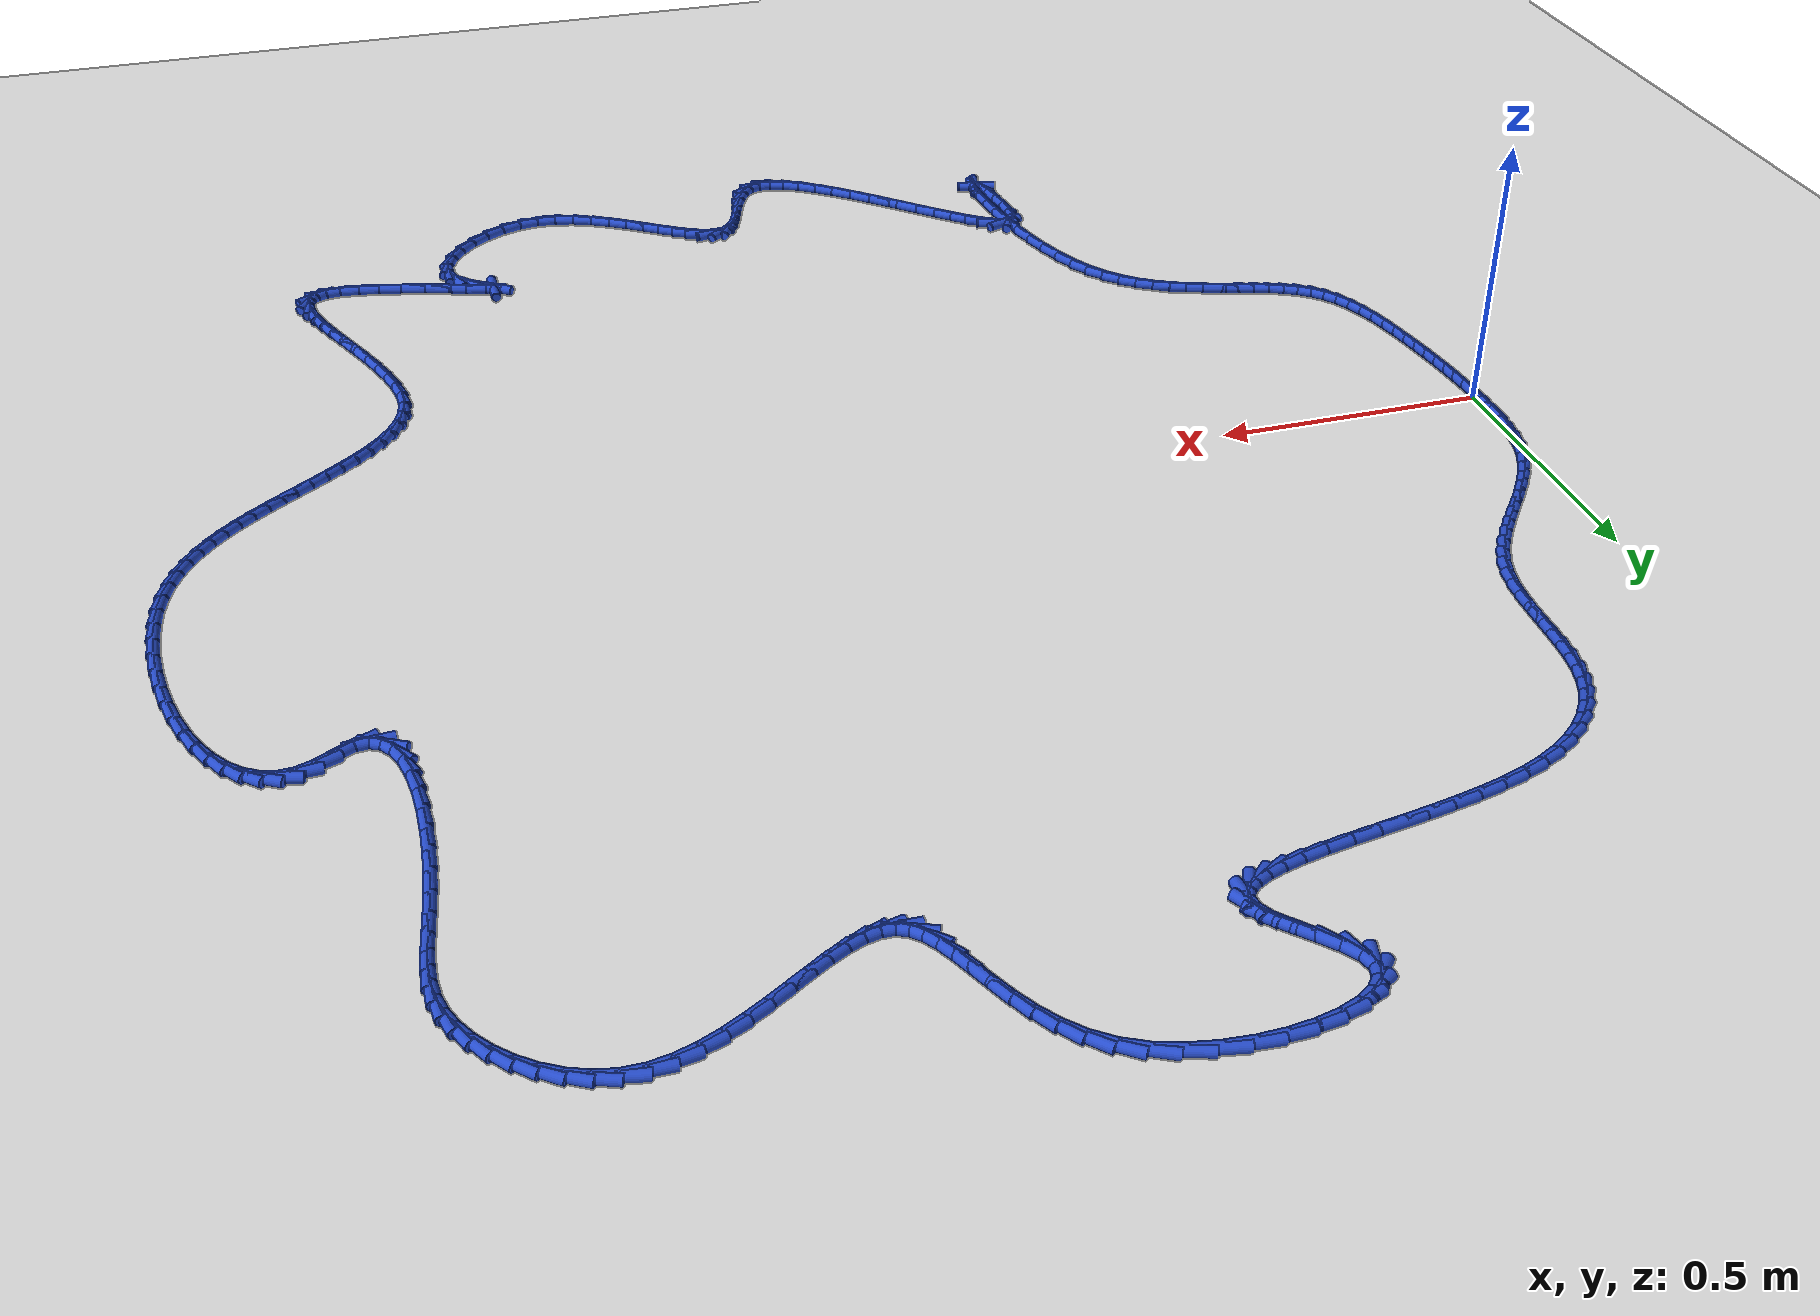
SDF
<sdf version="1.6">
 <world name="default">
  <light name="sun" type="directional">
   <pose>0 0 10 0 -0 0</pose>
   <diffuse>0.8 0.8 0.8 1</diffuse>
   <specular>0.2 0.2 0.2 1</specular>
   <attenuation>
    <range>1000</range>
    <constant>0.9</constant>
    <linear>0.01</linear>
    <quadratic>0.001</quadratic>
   </attenuation>
   <direction>-0.5 0.1 -0.9</direction>
  </light>
  <model name="ground_plane">
   <static>1</static>
   <link name="link">
    <collision name="collision">
     <geometry><plane><normal>0 0 1</normal><size>100 100</size></plane></geometry>
     <surface><friction><ode><mu>100</mu><mu2>50</mu2></ode></friction></surface>
    </collision>
    <visual name="visual">
     <cast_shadows>0</cast_shadows>
     <geometry><plane><normal>0 0 1</normal><size>100 100</size></plane></geometry>
     <material>
      <script><uri>file://media/materials/scripts/gazebo.material</uri><name>Gazebo/WhiteGlow</name></script>
     </material>
    </visual>
   </link>
  </model>
  <gravity>0 0 -9.8</gravity>
  <magnetic_field>6e-06 2.3e-05 -4.2e-05</magnetic_field>
  <atmosphere type="adiabatic"/>
  <physics name="default_physics" default="0" type="ode">
   <max_step_size>0.001</max_step_size>
   <real_time_factor>1</real_time_factor>
   <real_time_update_rate>1000</real_time_update_rate>
  </physics>
  <scene><ambient>0.4 0.4 0.4 1</ambient><background>0.7 0.7 0.7 1</background><shadows>1</shadows></scene>
  <spherical_coordinates>
   <surface_model>EARTH_WGS84</surface_model>
   <latitude_deg>0</latitude_deg>
   <longitude_deg>0</longitude_deg>
   <elevation>0</elevation>
   <heading_deg>0</heading_deg>
  </spherical_coordinates>
  <model name="line">
   <link name="link_0">
    <pose>1.1519648082658485e-18 6.938893903907228e-18 0.01 0 1.57 -1.5338162595452545</pose>
    <collision name="collision">
     <geometry><cylinder><radius>0.01</radius><length>0.08</length></cylinder></geometry>
    </collision>
    <visual name="visual">
     <material>
      <script><name>Gazebo/Blue</name><uri>file://media/materials/scripts/gazebo.material</uri></script>
     </material>
     <geometry><cylinder><radius>0.01</radius><length>0.08</length></cylinder></geometry>
    </visual>
   </link>
   <link name="link_1">
    <pose>-0.0011977544330981475 0.03237442454354316 0.01 0 1.57 -1.5638264975725031</pose>
    <collision name="collision">
     <geometry><cylinder><radius>0.01</radius><length>0.08</length></cylinder></geometry>
    </collision>
    <visual name="visual">
     <material>
      <script><name>Gazebo/Blue</name><uri>file://media/materials/scripts/gazebo.material</uri></script>
     </material>
     <geometry><cylinder><radius>0.01</radius><length>0.08</length></cylinder></geometry>
    </visual>
   </link>
   <link name="link_2">
    <pose>-0.0014253005337339182 0.0650211951810804 0.01 0 1.57 1.5364610037955164</pose>
    <collision name="collision">
     <geometry><cylinder><radius>0.01</radius><length>0.08</length></cylinder></geometry>
    </collision>
    <visual name="visual">
     <material>
      <script><name>Gazebo/Blue</name><uri>file://media/materials/scripts/gazebo.material</uri></script>
     </material>
     <geometry><cylinder><radius>0.01</radius><length>0.08</length></cylinder></geometry>
    </visual>
   </link>
   <link name="link_3">
    <pose>-0.0003037698806871436 0.0976724065553438 0.01 0 1.57 1.4830422235623202</pose>
    <collision name="collision">
     <geometry><cylinder><radius>0.01</radius><length>0.08</length></cylinder></geometry>
    </collision>
    <visual name="visual">
     <material>
      <script><name>Gazebo/Blue</name><uri>file://media/materials/scripts/gazebo.material</uri></script>
     </material>
     <geometry><cylinder><radius>0.01</radius><length>0.08</length></cylinder></geometry>
    </visual>
   </link>
   <link name="link_4">
    <pose>0.002545705947262344 0.13006015330906545 0.01 0 1.57 1.416451406037097</pose>
    <collision name="collision">
     <geometry><cylinder><radius>0.01</radius><length>0.08</length></cylinder></geometry>
    </collision>
    <visual name="visual">
     <material>
      <script><name>Gazebo/Blue</name><uri>file://media/materials/scripts/gazebo.material</uri></script>
     </material>
     <geometry><cylinder><radius>0.01</radius><length>0.08</length></cylinder></geometry>
    </visual>
   </link>
   <link name="link_5">
    <pose>0.0075019953713347165 0.16191653008497753 0.01 0 1.57 1.335608586323593</pose>
    <collision name="collision">
     <geometry><cylinder><radius>0.01</radius><length>0.08</length></cylinder></geometry>
    </collision>
    <visual name="visual">
     <material>
      <script><name>Gazebo/Blue</name><uri>file://media/materials/scripts/gazebo.material</uri></script>
     </material>
     <geometry><cylinder><radius>0.01</radius><length>0.08</length></cylinder></geometry>
    </visual>
   </link>
   <link name="link_6">
    <pose>0.014943966812750141 0.19297363152581193 0.01 0 1.57 1.2397752223210572</pose>
    <collision name="collision">
     <geometry><cylinder><radius>0.01</radius><length>0.08</length></cylinder></geometry>
    </collision>
    <visual name="visual">
     <material>
      <script><name>Gazebo/Blue</name><uri>file://media/materials/scripts/gazebo.material</uri></script>
     </material>
     <geometry><cylinder><radius>0.01</radius><length>0.08</length></cylinder></geometry>
    </visual>
   </link>
   <link name="link_7">
    <pose>0.025250488140888882 0.22296355256153097 0.01 0 1.57 1.135085195168869</pose>
    <collision name="collision">
     <geometry><cylinder><radius>0.01</radius><length>0.08</length></cylinder></geometry>
    </collision>
    <visual name="visual">
     <material>
      <script><name>Gazebo/Blue</name><uri>file://media/materials/scripts/gazebo.material</uri></script>
     </material>
     <geometry><cylinder><radius>0.01</radius><length>0.08</length></cylinder></geometry>
    </visual>
   </link>
   <link name="link_8">
    <pose>0.03863168303543045 0.25170621867577436 0.01 0 1.57 1.0456678746113428</pose>
    <collision name="collision">
     <geometry><cylinder><radius>0.01</radius><length>0.08</length></cylinder></geometry>
    </collision>
    <visual name="visual">
     <material>
      <script><name>Gazebo/Blue</name><uri>file://media/materials/scripts/gazebo.material</uri></script>
     </material>
     <geometry><cylinder><radius>0.01</radius><length>0.08</length></cylinder></geometry>
    </visual>
   </link>
   <link name="link_9">
    <pose>0.05465252050525628 0.27935735531094974 0.01 0 1.57 0.9774498484821887</pose>
    <collision name="collision">
     <geometry><cylinder><radius>0.01</radius><length>0.08</length></cylinder></geometry>
    </collision>
    <visual name="visual">
     <material>
      <script><name>Gazebo/Blue</name><uri>file://media/materials/scripts/gazebo.material</uri></script>
     </material>
     <geometry><cylinder><radius>0.01</radius><length>0.08</length></cylinder></geometry>
    </visual>
   </link>
   <link name="link_10">
    <pose>0.07272380981255602 0.3061529273294461 0.01 0 1.57 0.9297306780575509</pose>
    <collision name="collision">
     <geometry><cylinder><radius>0.01</radius><length>0.08</length></cylinder></geometry>
    </collision>
    <visual name="visual">
     <material>
      <script><name>Gazebo/Blue</name><uri>file://media/materials/scripts/gazebo.material</uri></script>
     </material>
     <geometry><cylinder><radius>0.01</radius><length>0.08</length></cylinder></geometry>
    </visual>
   </link>
   <link name="link_11">
    <pose>0.09225636021951933 0.332328899593652 0.01 0 1.57 0.9014986051978914</pose>
    <collision name="collision">
     <geometry><cylinder><radius>0.01</radius><length>0.08</length></cylinder></geometry>
    </collision>
    <visual name="visual">
     <material>
      <script><name>Gazebo/Blue</name><uri>file://media/materials/scripts/gazebo.material</uri></script>
     </material>
     <geometry><cylinder><radius>0.01</radius><length>0.08</length></cylinder></geometry>
    </visual>
   </link>
   <link name="link_12">
    <pose>0.11266098098833585 0.3581212369659564 0.01 0 1.57 0.8919845960247458</pose>
    <collision name="collision">
     <geometry><cylinder><radius>0.01</radius><length>0.08</length></cylinder></geometry>
    </collision>
    <visual name="visual">
     <material>
      <script><name>Gazebo/Blue</name><uri>file://media/materials/scripts/gazebo.material</uri></script>
     </material>
     <geometry><cylinder><radius>0.01</radius><length>0.08</length></cylinder></geometry>
    </visual>
   </link>
   <link name="link_13">
    <pose>0.13334848138119518 0.3837659043087477 0.01 0 1.57 0.9009361889354707</pose>
    <collision name="collision">
     <geometry><cylinder><radius>0.01</radius><length>0.08</length></cylinder></geometry>
    </collision>
    <visual name="visual">
     <material>
      <script><name>Gazebo/Blue</name><uri>file://media/materials/scripts/gazebo.material</uri></script>
     </material>
     <geometry><cylinder><radius>0.01</radius><length>0.08</length></cylinder></geometry>
    </visual>
   </link>
   <link name="link_14">
    <pose>0.153729670660287 0.40949886648441486 0.01 0 1.57 0.928702320163712</pose>
    <collision name="collision">
     <geometry><cylinder><radius>0.01</radius><length>0.08</length></cylinder></geometry>
    </collision>
    <visual name="visual">
     <material>
      <script><name>Gazebo/Blue</name><uri>file://media/materials/scripts/gazebo.material</uri></script>
     </material>
     <geometry><cylinder><radius>0.01</radius><length>0.08</length></cylinder></geometry>
    </visual>
   </link>
   <link name="link_15">
    <pose>0.17321535808780092 0.4355560883553464 0.01 0 1.57 0.9761640149685221</pose>
    <collision name="collision">
     <geometry><cylinder><radius>0.01</radius><length>0.08</length></cylinder></geometry>
    </collision>
    <visual name="visual">
     <material>
      <script><name>Gazebo/Blue</name><uri>file://media/materials/scripts/gazebo.material</uri></script>
     </material>
     <geometry><cylinder><radius>0.01</radius><length>0.08</length></cylinder></geometry>
    </visual>
   </link>
   <link name="link_16">
    <pose>0.1912163529259267 0.4621735347839316 0.01 0 1.57 1.044470331225712</pose>
    <collision name="collision">
     <geometry><cylinder><radius>0.01</radius><length>0.08</length></cylinder></geometry>
    </collision>
    <visual name="visual">
     <material>
      <script><name>Gazebo/Blue</name><uri>file://media/materials/scripts/gazebo.material</uri></script>
     </material>
     <geometry><cylinder><radius>0.01</radius><length>0.08</length></cylinder></geometry>
    </visual>
   </link>
   <link name="link_17">
    <pose>0.2071434644368538 0.4895871706325585 0.01 0 1.57 1.1344770753772226</pose>
    <collision name="collision">
     <geometry><cylinder><radius>0.01</radius><length>0.08</length></cylinder></geometry>
    </collision>
    <visual name="visual">
     <material>
      <script><name>Gazebo/Blue</name><uri>file://media/materials/scripts/gazebo.material</uri></script>
     </material>
     <geometry><cylinder><radius>0.01</radius><length>0.08</length></cylinder></geometry>
    </visual>
   </link>
   <link name="link_18">
    <pose>0.22040750188277203 0.5180329607636163 0.01 0 1.57 1.2455906043086944</pose>
    <collision name="collision">
     <geometry><cylinder><radius>0.01</radius><length>0.08</length></cylinder></geometry>
    </collision>
    <visual name="visual">
     <material>
      <script><name>Gazebo/Blue</name><uri>file://media/materials/scripts/gazebo.material</uri></script>
     </material>
     <geometry><cylinder><radius>0.01</radius><length>0.08</length></cylinder></geometry>
    </visual>
   </link>
   <link name="link_19">
    <pose>0.2304254790043768 0.5477443039159888 0.01 0 1.57 1.3588311836127835</pose>
    <collision name="collision">
     <geometry><cylinder><radius>0.01</radius><length>0.08</length></cylinder></geometry>
    </collision>
    <visual name="visual">
     <material>
      <script><name>Gazebo/Blue</name><uri>file://media/materials/scripts/gazebo.material</uri></script>
     </material>
     <geometry><cylinder><radius>0.01</radius><length>0.08</length></cylinder></geometry>
    </visual>
   </link>
   <link name="link_20">
    <pose>0.2370987548177766 0.5787542774325947 0.01 0 1.57 1.4448037140467622</pose>
    <collision name="collision">
     <geometry><cylinder><radius>0.01</radius><length>0.08</length></cylinder></geometry>
    </collision>
    <visual name="visual">
     <material>
      <script><name>Gazebo/Blue</name><uri>file://media/materials/scripts/gazebo.material</uri></script>
     </material>
     <geometry><cylinder><radius>0.01</radius><length>0.08</length></cylinder></geometry>
    </visual>
   </link>
   <link name="link_21">
    <pose>0.24115212927113275 0.6107553899641845 0.01 0 1.57 1.5023511678336026</pose>
    <collision name="collision">
     <geometry><cylinder><radius>0.01</radius><length>0.08</length></cylinder></geometry>
    </collision>
    <visual name="visual">
     <material>
      <script><name>Gazebo/Blue</name><uri>file://media/materials/scripts/gazebo.material</uri></script>
     </material>
     <geometry><cylinder><radius>0.01</radius><length>0.08</length></cylinder></geometry>
    </visual>
   </link>
   <link name="link_22">
    <pose>0.24339047266090846 0.6434070336952997 0.01 0 1.57 1.533552506006652</pose>
    <collision name="collision">
     <geometry><cylinder><radius>0.01</radius><length>0.08</length></cylinder></geometry>
    </collision>
    <visual name="visual">
     <material>
      <script><name>Gazebo/Blue</name><uri>file://media/materials/scripts/gazebo.material</uri></script>
     </material>
     <geometry><cylinder><radius>0.01</radius><length>0.08</length></cylinder></geometry>
    </visual>
   </link>
   <link name="link_23">
    <pose>0.24461865528356658 0.676368600810481 0.01 0 1.57 1.5397445211642842</pose>
    <collision name="collision">
     <geometry><cylinder><radius>0.01</radius><length>0.08</length></cylinder></geometry>
    </collision>
    <visual name="visual">
     <material>
      <script><name>Gazebo/Blue</name><uri>file://media/materials/scripts/gazebo.material</uri></script>
     </material>
     <geometry><cylinder><radius>0.01</radius><length>0.08</length></cylinder></geometry>
    </visual>
   </link>
   <link name="link_24">
    <pose>0.24564154743557015 0.7092994834942695 0.01 0 1.57 1.5210066634106196</pose>
    <collision name="collision">
     <geometry><cylinder><radius>0.01</radius><length>0.08</length></cylinder></geometry>
    </collision>
    <visual name="visual">
     <material>
      <script><name>Gazebo/Blue</name><uri>file://media/materials/scripts/gazebo.material</uri></script>
     </material>
     <geometry><cylinder><radius>0.01</radius><length>0.08</length></cylinder></geometry>
    </visual>
   </link>
   <link name="link_25">
    <pose>0.24726401941338239 0.7418590739312065 0.01 0 1.57 1.476037278993582</pose>
    <collision name="collision">
     <geometry><cylinder><radius>0.01</radius><length>0.08</length></cylinder></geometry>
    </collision>
    <visual name="visual">
     <material>
      <script><name>Gazebo/Blue</name><uri>file://media/materials/scripts/gazebo.material</uri></script>
     </material>
     <geometry><cylinder><radius>0.01</radius><length>0.08</length></cylinder></geometry>
    </visual>
   </link>
   <link name="link_26">
    <pose>0.25029094151346604 0.7737067643058326 0.01 0 1.57 1.402372668532106</pose>
    <collision name="collision">
     <geometry><cylinder><radius>0.01</radius><length>0.08</length></cylinder></geometry>
    </collision>
    <visual name="visual">
     <material>
      <script><name>Gazebo/Blue</name><uri>file://media/materials/scripts/gazebo.material</uri></script>
     </material>
     <geometry><cylinder><radius>0.01</radius><length>0.08</length></cylinder></geometry>
    </visual>
   </link>
   <link name="link_27">
    <pose>0.2555271840322842 0.8045019468026888 0.01 0 1.57 1.2973821305707063</pose>
    <collision name="collision">
     <geometry><cylinder><radius>0.01</radius><length>0.08</length></cylinder></geometry>
    </collision>
    <visual name="visual">
     <material>
      <script><name>Gazebo/Blue</name><uri>file://media/materials/scripts/gazebo.material</uri></script>
     </material>
     <geometry><cylinder><radius>0.01</radius><length>0.08</length></cylinder></geometry>
    </visual>
   </link>
   <link name="link_28">
    <pose>0.26377307075466094 0.83390561649291 0.01 0 1.57 1.1700862440797273</pose>
    <collision name="collision">
     <geometry><cylinder><radius>0.01</radius><length>0.08</length></cylinder></geometry>
    </collision>
    <visual name="visual">
     <material>
      <script><name>Gazebo/Blue</name><uri>file://media/materials/scripts/gazebo.material</uri></script>
     </material>
     <geometry><cylinder><radius>0.01</radius><length>0.08</length></cylinder></geometry>
    </visual>
   </link>
   <link name="link_29">
    <pose>0.2755394894066221 0.8616808100159998 0.01 0 1.57 1.0389793840416084</pose>
    <collision name="collision">
     <geometry><cylinder><radius>0.01</radius><length>0.08</length></cylinder></geometry>
    </collision>
    <visual name="visual">
     <material>
      <script><name>Gazebo/Blue</name><uri>file://media/materials/scripts/gazebo.material</uri></script>
     </material>
     <geometry><cylinder><radius>0.01</radius><length>0.08</length></cylinder></geometry>
    </visual>
   </link>
   <link name="link_30">
    <pose>0.29087885961140364 0.8877521983442789 0.01 0 1.57 0.909265815269875</pose>
    <collision name="collision">
     <geometry><cylinder><radius>0.01</radius><length>0.08</length></cylinder></geometry>
    </collision>
    <visual name="visual">
     <material>
      <script><name>Gazebo/Blue</name><uri>file://media/materials/scripts/gazebo.material</uri></script>
     </material>
     <geometry><cylinder><radius>0.01</radius><length>0.08</length></cylinder></geometry>
    </visual>
   </link>
   <link name="link_31">
    <pose>0.3098029896846998 0.9120587700908345 0.01 0 1.57 0.7845103147579487</pose>
    <collision name="collision">
     <geometry><cylinder><radius>0.01</radius><length>0.08</length></cylinder></geometry>
    </collision>
    <visual name="visual">
     <material>
      <script><name>Gazebo/Blue</name><uri>file://media/materials/scripts/gazebo.material</uri></script>
     </material>
     <geometry><cylinder><radius>0.01</radius><length>0.08</length></cylinder></geometry>
    </visual>
   </link>
   <link name="link_32">
    <pose>0.33232368794220474 0.9345395138687543 0.01 0 1.57 0.6674799219659406</pose>
    <collision name="collision">
     <geometry><cylinder><radius>0.01</radius><length>0.08</length></cylinder></geometry>
    </collision>
    <visual name="visual">
     <material>
      <script><name>Gazebo/Blue</name><uri>file://media/materials/scripts/gazebo.material</uri></script>
     </material>
     <geometry><cylinder><radius>0.01</radius><length>0.08</length></cylinder></geometry>
    </visual>
   </link>
   <link name="link_33">
    <pose>0.35845276269961285 0.9551334182911259 0.01 0 1.57 0.5598737728286589</pose>
    <collision name="collision">
     <geometry><cylinder><radius>0.01</radius><length>0.08</length></cylinder></geometry>
    </collision>
    <visual name="visual">
     <material>
      <script><name>Gazebo/Blue</name><uri>file://media/materials/scripts/gazebo.material</uri></script>
     </material>
     <geometry><cylinder><radius>0.01</radius><length>0.08</length></cylinder></geometry>
    </visual>
   </link>
   <link name="link_34">
    <pose>0.38820202227261824 0.9737794719710365 0.01 0 1.57 0.462366194935475</pose>
    <collision name="collision">
     <geometry><cylinder><radius>0.01</radius><length>0.08</length></cylinder></geometry>
    </collision>
    <visual name="visual">
     <material>
      <script><name>Gazebo/Blue</name><uri>file://media/materials/scripts/gazebo.material</uri></script>
     </material>
     <geometry><cylinder><radius>0.01</radius><length>0.08</length></cylinder></geometry>
    </visual>
   </link>
   <link name="link_35">
    <pose>0.4215832749769152 0.9904166635215741 0.01 0 1.57 0.3748559651297808</pose>
    <collision name="collision">
     <geometry><cylinder><radius>0.01</radius><length>0.08</length></cylinder></geometry>
    </collision>
    <visual name="visual">
     <material>
      <script><name>Gazebo/Blue</name><uri>file://media/materials/scripts/gazebo.material</uri></script>
     </material>
     <geometry><cylinder><radius>0.01</radius><length>0.08</length></cylinder></geometry>
    </visual>
   </link>
   <link name="link_36">
    <pose>0.4586076440816507 1.0049842804329159 0.01 0 1.57 0.3005961824647087</pose>
    <collision name="collision">
     <geometry><cylinder><radius>0.01</radius><length>0.08</length></cylinder></geometry>
    </collision>
    <visual name="visual">
     <material>
      <script><name>Gazebo/Blue</name><uri>file://media/materials/scripts/gazebo.material</uri></script>
     </material>
     <geometry><cylinder><radius>0.01</radius><length>0.08</length></cylinder></geometry>
    </visual>
   </link>
   <link name="link_37">
    <pose>0.49905495005863604 1.0175225246619781 0.01 0 1.57 0.2455334116099302</pose>
    <collision name="collision">
     <geometry><cylinder><radius>0.01</radius><length>0.08</length></cylinder></geometry>
    </collision>
    <visual name="visual">
     <material>
      <script><name>Gazebo/Blue</name><uri>file://media/materials/scripts/gazebo.material</uri></script>
     </material>
     <geometry><cylinder><radius>0.01</radius><length>0.08</length></cylinder></geometry>
    </visual>
   </link>
   <link name="link_38">
    <pose>0.5421384283040468 1.0283187920233734 0.01 0 1.57 0.20615525021939676</pose>
    <collision name="collision">
     <geometry><cylinder><radius>0.01</radius><length>0.08</length></cylinder></geometry>
    </collision>
    <visual name="visual">
     <material>
      <script><name>Gazebo/Blue</name><uri>file://media/materials/scripts/gazebo.material</uri></script>
     </material>
     <geometry><cylinder><radius>0.01</radius><length>0.08</length></cylinder></geometry>
    </visual>
   </link>
   <link name="link_39">
    <pose>0.5869861566062353 1.0376976315122262 0.01 0 1.57 0.1792097871674355</pose>
    <collision name="collision">
     <geometry><cylinder><radius>0.01</radius><length>0.08</length></cylinder></geometry>
    </collision>
    <visual name="visual">
     <material>
      <script><name>Gazebo/Blue</name><uri>file://media/materials/scripts/gazebo.material</uri></script>
     </material>
     <geometry><cylinder><radius>0.01</radius><length>0.08</length></cylinder></geometry>
    </visual>
   </link>
   <link name="link_40">
    <pose>0.6327262127535523 1.0459835921236607 0.01 0 1.57 0.16282779220886007</pose>
    <collision name="collision">
     <geometry><cylinder><radius>0.01</radius><length>0.08</length></cylinder></geometry>
    </collision>
    <visual name="visual">
     <material>
      <script><name>Gazebo/Blue</name><uri>file://media/materials/scripts/gazebo.material</uri></script>
     </material>
     <geometry><cylinder><radius>0.01</radius><length>0.08</length></cylinder></geometry>
    </visual>
   </link>
   <link name="link_41">
    <pose>0.6784866745343503 1.0535012228528013 0.01 0 1.57 0.15623173205487667</pose>
    <collision name="collision">
     <geometry><cylinder><radius>0.01</radius><length>0.08</length></cylinder></geometry>
    </collision>
    <visual name="visual">
     <material>
      <script><name>Gazebo/Blue</name><uri>file://media/materials/scripts/gazebo.material</uri></script>
     </material>
     <geometry><cylinder><radius>0.01</radius><length>0.08</length></cylinder></geometry>
    </visual>
   </link>
   <link name="link_42">
    <pose>0.7233956197369801 1.0605750726947727 0.01 0 1.57 0.15966967953347624</pose>
    <collision name="collision">
     <geometry><cylinder><radius>0.01</radius><length>0.08</length></cylinder></geometry>
    </collision>
    <visual name="visual">
     <material>
      <script><name>Gazebo/Blue</name><uri>file://media/materials/scripts/gazebo.material</uri></script>
     </material>
     <geometry><cylinder><radius>0.01</radius><length>0.08</length></cylinder></geometry>
    </visual>
   </link>
   <link name="link_43">
    <pose>0.7665811261497935 1.0675296906446987 0.01 0 1.57 0.17459976128015814</pose>
    <collision name="collision">
     <geometry><cylinder><radius>0.01</radius><length>0.08</length></cylinder></geometry>
    </collision>
    <visual name="visual">
     <material>
      <script><name>Gazebo/Blue</name><uri>file://media/materials/scripts/gazebo.material</uri></script>
     </material>
     <geometry><cylinder><radius>0.01</radius><length>0.08</length></cylinder></geometry>
    </visual>
   </link>
   <link name="link_44">
    <pose>0.8071712715611429 1.0746896256977045 0.01 0 1.57 0.20425585236347724</pose>
    <collision name="collision">
     <geometry><cylinder><radius>0.01</radius><length>0.08</length></cylinder></geometry>
    </collision>
    <visual name="visual">
     <material>
      <script><name>Gazebo/Blue</name><uri>file://media/materials/scripts/gazebo.material</uri></script>
     </material>
     <geometry><cylinder><radius>0.01</radius><length>0.08</length></cylinder></geometry>
    </visual>
   </link>
   <link name="link_45">
    <pose>0.8442941337593788 1.0823794268489142 0.01 0 1.57 0.2549527005088165</pose>
    <collision name="collision">
     <geometry><cylinder><radius>0.01</radius><length>0.08</length></cylinder></geometry>
    </collision>
    <visual name="visual">
     <material>
      <script><name>Gazebo/Blue</name><uri>file://media/materials/scripts/gazebo.material</uri></script>
     </material>
     <geometry><cylinder><radius>0.01</radius><length>0.08</length></cylinder></geometry>
    </visual>
   </link>
   <link name="link_46">
    <pose>0.8770777905328535 1.090923643093452 0.01 0 1.57 0.3390248917568101</pose>
    <collision name="collision">
     <geometry><cylinder><radius>0.01</radius><length>0.08</length></cylinder></geometry>
    </collision>
    <visual name="visual">
     <material>
      <script><name>Gazebo/Blue</name><uri>file://media/materials/scripts/gazebo.material</uri></script>
     </material>
     <geometry><cylinder><radius>0.01</radius><length>0.08</length></cylinder></geometry>
    </visual>
   </link>
   <link name="link_47">
    <pose>0.9046503196699183 1.1006468234264424 0.01 0 1.57 0.48142815267958466</pose>
    <collision name="collision">
     <geometry><cylinder><radius>0.01</radius><length>0.08</length></cylinder></geometry>
    </collision>
    <visual name="visual">
     <material>
      <script><name>Gazebo/Blue</name><uri>file://media/materials/scripts/gazebo.material</uri></script>
     </material>
     <geometry><cylinder><radius>0.01</radius><length>0.08</length></cylinder></geometry>
    </visual>
   </link>
   <link name="link_48">
    <pose>0.926139798958925 1.1118735168430103 0.01 0 1.57 0.731814446814402</pose>
    <collision name="collision">
     <geometry><cylinder><radius>0.01</radius><length>0.08</length></cylinder></geometry>
    </collision>
    <visual name="visual">
     <material>
      <script><name>Gazebo/Blue</name><uri>file://media/materials/scripts/gazebo.material</uri></script>
     </material>
     <geometry><cylinder><radius>0.01</radius><length>0.08</length></cylinder></geometry>
    </visual>
   </link>
   <link name="link_49">
    <pose>0.9406743061882248 1.1249282723382792 0.01 0 1.57 1.155387865178105</pose>
    <collision name="collision">
     <geometry><cylinder><radius>0.01</radius><length>0.08</length></cylinder></geometry>
    </collision>
    <visual name="visual">
     <material>
      <script><name>Gazebo/Blue</name><uri>file://media/materials/scripts/gazebo.material</uri></script>
     </material>
     <geometry><cylinder><radius>0.01</radius><length>0.08</length></cylinder></geometry>
    </visual>
   </link>
   <link name="link_50">
    <pose>0.9473819191461701 1.1401356389073745 0.01 0 1.57 -1.4586727570723999</pose>
    <collision name="collision">
     <geometry><cylinder><radius>0.01</radius><length>0.08</length></cylinder></geometry>
    </collision>
    <visual name="visual">
     <material>
      <script><name>Gazebo/Blue</name><uri>file://media/materials/scripts/gazebo.material</uri></script>
     </material>
     <geometry><cylinder><radius>0.01</radius><length>0.08</length></cylinder></geometry>
    </visual>
   </link>
   <link name="link_51">
    <pose>0.9453907156211117 1.1578201655454199 0.01 0 1.57 -1.057074999462949</pose>
    <collision name="collision">
     <geometry><cylinder><radius>0.01</radius><length>0.08</length></cylinder></geometry>
    </collision>
    <visual name="visual">
     <material>
      <script><name>Gazebo/Blue</name><uri>file://media/materials/scripts/gazebo.material</uri></script>
     </material>
     <geometry><cylinder><radius>0.01</radius><length>0.08</length></cylinder></geometry>
    </visual>
   </link>
   <link name="link_52">
    <pose>0.9338316665987543 1.178305686006102 0.01 0 1.57 -0.8479654065867887</pose>
    <collision name="collision">
     <geometry><cylinder><radius>0.01</radius><length>0.08</length></cylinder></geometry>
    </collision>
    <visual name="visual">
     <material>
      <script><name>Gazebo/Blue</name><uri>file://media/materials/scripts/gazebo.material</uri></script>
     </material>
     <geometry><cylinder><radius>0.01</radius><length>0.08</length></cylinder></geometry>
    </visual>
   </link>
   <link name="link_53">
    <pose>0.9133313871890353 1.2015462885595396 0.01 0 1.57 -0.7873486888170741</pose>
    <collision name="collision">
     <geometry><cylinder><radius>0.01</radius><length>0.08</length></cylinder></geometry>
    </collision>
    <visual name="visual">
     <material>
      <script><name>Gazebo/Blue</name><uri>file://media/materials/scripts/gazebo.material</uri></script>
     </material>
     <geometry><cylinder><radius>0.01</radius><length>0.08</length></cylinder></geometry>
    </visual>
   </link>
   <link name="link_54">
    <pose>0.8884517037724283 1.2265232186915362 0.01 0 1.57 -0.8152047304556284</pose>
    <collision name="collision">
     <geometry><cylinder><radius>0.01</radius><length>0.08</length></cylinder></geometry>
    </collision>
    <visual name="visual">
     <material>
      <script><name>Gazebo/Blue</name><uri>file://media/materials/scripts/gazebo.material</uri></script>
     </material>
     <geometry><cylinder><radius>0.01</radius><length>0.08</length></cylinder></geometry>
    </visual>
   </link>
   <link name="link_55">
    <pose>0.8643939701368678 1.2520596211962296 0.01 0 1.57 -0.9443266670071779</pose>
    <collision name="collision">
     <geometry><cylinder><radius>0.01</radius><length>0.08</length></cylinder></geometry>
    </collision>
    <visual name="visual">
     <material>
      <script><name>Gazebo/Blue</name><uri>file://media/materials/scripts/gazebo.material</uri></script>
     </material>
     <geometry><cylinder><radius>0.01</radius><length>0.08</length></cylinder></geometry>
    </visual>
   </link>
   <link name="link_56">
    <pose>0.8463595400702895 1.276978640867758 0.01 0 1.57 -1.2756371198639962</pose>
    <collision name="collision">
     <geometry><cylinder><radius>0.01</radius><length>0.08</length></cylinder></geometry>
    </collision>
    <visual name="visual">
     <material>
      <script><name>Gazebo/Blue</name><uri>file://media/materials/scripts/gazebo.material</uri></script>
     </material>
     <geometry><cylinder><radius>0.01</radius><length>0.08</length></cylinder></geometry>
    </visual>
   </link>
   <link name="link_57">
    <pose>0.8393194399337724 1.3001338079470532 0.01 0 1.57 1.3215550835016123</pose>
    <collision name="collision">
     <geometry><cylinder><radius>0.01</radius><length>0.08</length></cylinder></geometry>
    </collision>
    <visual name="visual">
     <material>
      <script><name>Gazebo/Blue</name><uri>file://media/materials/scripts/gazebo.material</uri></script>
     </material>
     <geometry><cylinder><radius>0.01</radius><length>0.08</length></cylinder></geometry>
    </visual>
   </link>
   <link name="link_58">
    <pose>0.8445949910264087 1.3208601321084388 0.01 0 1.57 0.8447809884516944</pose>
    <collision name="collision">
     <geometry><cylinder><radius>0.01</radius><length>0.08</length></cylinder></geometry>
    </collision>
    <visual name="visual">
     <material>
      <script><name>Gazebo/Blue</name><uri>file://media/materials/scripts/gazebo.material</uri></script>
     </material>
     <geometry><cylinder><radius>0.01</radius><length>0.08</length></cylinder></geometry>
    </visual>
   </link>
   <link name="link_59">
    <pose>0.860590202516286 1.3388774831089025 0.01 0 1.57 0.5409068925253919</pose>
    <collision name="collision">
     <geometry><cylinder><radius>0.01</radius><length>0.08</length></cylinder></geometry>
    </collision>
    <visual name="visual">
     <material>
      <script><name>Gazebo/Blue</name><uri>file://media/materials/scripts/gazebo.material</uri></script>
     </material>
     <geometry><cylinder><radius>0.01</radius><length>0.08</length></cylinder></geometry>
    </visual>
   </link>
   <link name="link_60">
    <pose>0.8856275422159168 1.353916487872111 0.01 0 1.57 0.349009854665366</pose>
    <collision name="collision">
     <geometry><cylinder><radius>0.01</radius><length>0.08</length></cylinder></geometry>
    </collision>
    <visual name="visual">
     <material>
      <script><name>Gazebo/Blue</name><uri>file://media/materials/scripts/gazebo.material</uri></script>
     </material>
     <geometry><cylinder><radius>0.01</radius><length>0.08</length></cylinder></geometry>
    </visual>
   </link>
   <link name="link_61">
    <pose>0.9180294779378143 1.3657077733217313 0.01 0 1.57 0.213909653808524</pose>
    <collision name="collision">
     <geometry><cylinder><radius>0.01</radius><length>0.08</length></cylinder></geometry>
    </collision>
    <visual name="visual">
     <material>
      <script><name>Gazebo/Blue</name><uri>file://media/materials/scripts/gazebo.material</uri></script>
     </material>
     <geometry><cylinder><radius>0.01</radius><length>0.08</length></cylinder></geometry>
    </visual>
   </link>
   <link name="link_62">
    <pose>0.9561184774944903 1.3739819663814297 0.01 0 1.57 0.10619951335669156</pose>
    <collision name="collision">
     <geometry><cylinder><radius>0.01</radius><length>0.08</length></cylinder></geometry>
    </collision>
    <visual name="visual">
     <material>
      <script><name>Gazebo/Blue</name><uri>file://media/materials/scripts/gazebo.material</uri></script>
     </material>
     <geometry><cylinder><radius>0.01</radius><length>0.08</length></cylinder></geometry>
    </visual>
   </link>
   <link name="link_63">
    <pose>0.9982170086984588 1.3784696939748728 0.01 0 1.57 0.009720240614919409</pose>
    <collision name="collision">
     <geometry><cylinder><radius>0.01</radius><length>0.08</length></cylinder></geometry>
    </collision>
    <visual name="visual">
     <material>
      <script><name>Gazebo/Blue</name><uri>file://media/materials/scripts/gazebo.material</uri></script>
     </material>
     <geometry><cylinder><radius>0.01</radius><length>0.08</length></cylinder></geometry>
    </visual>
   </link>
   <link name="link_64">
    <pose>1.0426475393622312 1.3789015830257279 0.01 0 1.57 -0.08614146693852491</pose>
    <collision name="collision">
     <geometry><cylinder><radius>0.01</radius><length>0.08</length></cylinder></geometry>
    </collision>
    <visual name="visual">
     <material>
      <script><name>Gazebo/Blue</name><uri>file://media/materials/scripts/gazebo.material</uri></script>
     </material>
     <geometry><cylinder><radius>0.01</radius><length>0.08</length></cylinder></geometry>
    </visual>
   </link>
   <link name="link_65">
    <pose>1.0877325372983209 1.3750082604576612 0.01 0 1.57 -0.1903047087714762</pose>
    <collision name="collision">
     <geometry><cylinder><radius>0.01</radius><length>0.08</length></cylinder></geometry>
    </collision>
    <visual name="visual">
     <material>
      <script><name>Gazebo/Blue</name><uri>file://media/materials/scripts/gazebo.material</uri></script>
     </material>
     <geometry><cylinder><radius>0.01</radius><length>0.08</length></cylinder></geometry>
    </visual>
   </link>
   <link name="link_66">
    <pose>1.131794470319241 1.3665203531943397 0.01 0 1.57 -0.31225011246614415</pose>
    <collision name="collision">
     <geometry><cylinder><radius>0.01</radius><length>0.08</length></cylinder></geometry>
    </collision>
    <visual name="visual">
     <material>
      <script><name>Gazebo/Blue</name><uri>file://media/materials/scripts/gazebo.material</uri></script>
     </material>
     <geometry><cylinder><radius>0.01</radius><length>0.08</length></cylinder></geometry>
    </visual>
   </link>
   <link name="link_67">
    <pose>1.1731558062375036 1.35316848815943 0.01 0 1.57 -0.4634792031064176</pose>
    <collision name="collision">
     <geometry><cylinder><radius>0.01</radius><length>0.08</length></cylinder></geometry>
    </collision>
    <visual name="visual">
     <material>
      <script><name>Gazebo/Blue</name><uri>file://media/materials/scripts/gazebo.material</uri></script>
     </material>
     <geometry><cylinder><radius>0.01</radius><length>0.08</length></cylinder></geometry>
    </visual>
   </link>
   <link name="link_68">
    <pose>1.2101402603611515 1.3346840459422666 0.01 0 1.57 -0.6405506658462718</pose>
    <collision name="collision">
     <geometry><cylinder><radius>0.01</radius><length>0.08</length></cylinder></geometry>
    </collision>
    <visual name="visual">
     <material>
      <script><name>Gazebo/Blue</name><uri>file://media/materials/scripts/gazebo.material</uri></script>
     </material>
     <geometry><cylinder><radius>0.01</radius><length>0.08</length></cylinder></geometry>
    </visual>
   </link>
   <link name="link_69">
    <pose>1.2416861663648582 1.3111697245043037 0.01 0 1.57 -0.8005669810562018</pose>
    <collision name="collision">
     <geometry><cylinder><radius>0.01</radius><length>0.08</length></cylinder></geometry>
    </collision>
    <visual name="visual">
     <material>
      <script><name>Gazebo/Blue</name><uri>file://media/materials/scripts/gazebo.material</uri></script>
     </material>
     <geometry><cylinder><radius>0.01</radius><length>0.08</length></cylinder></geometry>
    </visual>
   </link>
   <link name="link_70">
    <pose>1.2683369347292894 1.283697917693104 0.01 0 1.57 -0.9292614443777474</pose>
    <collision name="collision">
     <geometry><cylinder><radius>0.01</radius><length>0.08</length></cylinder></geometry>
    </collision>
    <visual name="visual">
     <material>
      <script><name>Gazebo/Blue</name><uri>file://media/materials/scripts/gazebo.material</uri></script>
     </material>
     <geometry><cylinder><radius>0.01</radius><length>0.08</length></cylinder></geometry>
    </visual>
   </link>
   <link name="link_71">
    <pose>1.2908947221284324 1.2534973390527564 0.01 0 1.57 -1.0246770198170472</pose>
    <collision name="collision">
     <geometry><cylinder><radius>0.01</radius><length>0.08</length></cylinder></geometry>
    </collision>
    <visual name="visual">
     <material>
      <script><name>Gazebo/Blue</name><uri>file://media/materials/scripts/gazebo.material</uri></script>
     </material>
     <geometry><cylinder><radius>0.01</radius><length>0.08</length></cylinder></geometry>
    </visual>
   </link>
   <link name="link_72">
    <pose>1.3101616852362756 1.221796702127349 0.01 0 1.57 -1.0875208500829896</pose>
    <collision name="collision">
     <geometry><cylinder><radius>0.01</radius><length>0.08</length></cylinder></geometry>
    </collision>
    <visual name="visual">
     <material>
      <script><name>Gazebo/Blue</name><uri>file://media/materials/scripts/gazebo.material</uri></script>
     </material>
     <geometry><cylinder><radius>0.01</radius><length>0.08</length></cylinder></geometry>
    </visual>
   </link>
   <link name="link_73">
    <pose>1.3269399807268067 1.1898247204609698 0.01 0 1.57 -1.1179241420468402</pose>
    <collision name="collision">
     <geometry><cylinder><radius>0.01</radius><length>0.08</length></cylinder></geometry>
    </collision>
    <visual name="visual">
     <material>
      <script><name>Gazebo/Blue</name><uri>file://media/materials/scripts/gazebo.material</uri></script>
     </material>
     <geometry><cylinder><radius>0.01</radius><length>0.08</length></cylinder></geometry>
    </visual>
   </link>
   <link name="link_74">
    <pose>1.3420317652740137 1.158810107597707 0.01 0 1.57 -1.1129049039712045</pose>
    <collision name="collision">
     <geometry><cylinder><radius>0.01</radius><length>0.08</length></cylinder></geometry>
    </collision>
    <visual name="visual">
     <material>
      <script><name>Gazebo/Blue</name><uri>file://media/materials/scripts/gazebo.material</uri></script>
     </material>
     <geometry><cylinder><radius>0.01</radius><length>0.08</length></cylinder></geometry>
    </visual>
   </link>
   <link name="link_75">
    <pose>1.3562391955518842 1.1299815770816495 0.01 0 1.57 -1.0635026626829978</pose>
    <collision name="collision">
     <geometry><cylinder><radius>0.01</radius><length>0.08</length></cylinder></geometry>
    </collision>
    <visual name="visual">
     <material>
      <script><name>Gazebo/Blue</name><uri>file://media/materials/scripts/gazebo.material</uri></script>
     </material>
     <geometry><cylinder><radius>0.01</radius><length>0.08</length></cylinder></geometry>
    </visual>
   </link>
   <link name="link_76">
    <pose>1.3703644282344074 1.1045678424568854 0.01 0 1.57 -0.9502498864761191</pose>
    <collision name="collision">
     <geometry><cylinder><radius>0.01</radius><length>0.08</length></cylinder></geometry>
    </collision>
    <visual name="visual">
     <material>
      <script><name>Gazebo/Blue</name><uri>file://media/materials/scripts/gazebo.material</uri></script>
     </material>
     <geometry><cylinder><radius>0.01</radius><length>0.08</length></cylinder></geometry>
    </visual>
   </link>
   <link name="link_77">
    <pose>1.3852096199955704 1.0837976172675026 0.01 0 1.57 -0.73843796721582</pose>
    <collision name="collision">
     <geometry><cylinder><radius>0.01</radius><length>0.08</length></cylinder></geometry>
    </collision>
    <visual name="visual">
     <material>
      <script><name>Gazebo/Blue</name><uri>file://media/materials/scripts/gazebo.material</uri></script>
     </material>
     <geometry><cylinder><radius>0.01</radius><length>0.08</length></cylinder></geometry>
    </visual>
   </link>
   <link name="link_78">
    <pose>1.401576927509361 1.068899615057589 0.01 0 1.57 -0.39695741105109433</pose>
    <collision name="collision">
     <geometry><cylinder><radius>0.01</radius><length>0.08</length></cylinder></geometry>
    </collision>
    <visual name="visual">
     <material>
      <script><name>Gazebo/Blue</name><uri>file://media/materials/scripts/gazebo.material</uri></script>
     </material>
     <geometry><cylinder><radius>0.01</radius><length>0.08</length></cylinder></geometry>
    </visual>
   </link>
   <link name="link_79">
    <pose>1.4202539553745168 1.0610699929710747 0.01 0 1.57 -0.02797339589513108</pose>
    <collision name="collision">
     <geometry><cylinder><radius>0.01</radius><length>0.08</length></cylinder></geometry>
    </collision>
    <visual name="visual">
     <material>
      <script><name>Gazebo/Blue</name><uri>file://media/materials/scripts/gazebo.material</uri></script>
     </material>
     <geometry><cylinder><radius>0.01</radius><length>0.08</length></cylinder></geometry>
    </visual>
   </link>
   <link name="link_80">
    <pose>1.441567346755273 1.0604736294743564 0.01 0 1.57 0.23108343504771459</pose>
    <collision name="collision">
     <geometry><cylinder><radius>0.01</radius><length>0.08</length></cylinder></geometry>
    </collision>
    <visual name="visual">
     <material>
      <script><name>Gazebo/Blue</name><uri>file://media/materials/scripts/gazebo.material</uri></script>
     </material>
     <geometry><cylinder><radius>0.01</radius><length>0.08</length></cylinder></geometry>
    </visual>
   </link>
   <link name="link_81">
    <pose>1.4652993423868723 1.0660574473113065 0.01 0 1.57 0.3897947270925956</pose>
    <collision name="collision">
     <geometry><cylinder><radius>0.01</radius><length>0.08</length></cylinder></geometry>
    </collision>
    <visual name="visual">
     <material>
      <script><name>Gazebo/Blue</name><uri>file://media/materials/scripts/gazebo.material</uri></script>
     </material>
     <geometry><cylinder><radius>0.01</radius><length>0.08</length></cylinder></geometry>
    </visual>
   </link>
   <link name="link_82">
    <pose>1.491200797790045 1.0766981531510995 0.01 0 1.57 0.4825412748929228</pose>
    <collision name="collision">
     <geometry><cylinder><radius>0.01</radius><length>0.08</length></cylinder></geometry>
    </collision>
    <visual name="visual">
     <material>
      <script><name>Gazebo/Blue</name><uri>file://media/materials/scripts/gazebo.material</uri></script>
     </material>
     <geometry><cylinder><radius>0.01</radius><length>0.08</length></cylinder></geometry>
    </visual>
   </link>
   <link name="link_83">
    <pose>1.5190225684855183 1.0912724536629084 0.01 0 1.57 0.5326257153427971</pose>
    <collision name="collision">
     <geometry><cylinder><radius>0.01</radius><length>0.08</length></cylinder></geometry>
    </collision>
    <visual name="visual">
     <material>
      <script><name>Gazebo/Blue</name><uri>file://media/materials/scripts/gazebo.material</uri></script>
     </material>
     <geometry><cylinder><radius>0.01</radius><length>0.08</length></cylinder></geometry>
    </visual>
   </link>
   <link name="link_84">
    <pose>1.5485155099940222 1.1086570555159072 0.01 0 1.57 0.5527572748742934</pose>
    <collision name="collision">
     <geometry><cylinder><radius>0.01</radius><length>0.08</length></cylinder></geometry>
    </collision>
    <visual name="visual">
     <material>
      <script><name>Gazebo/Blue</name><uri>file://media/materials/scripts/gazebo.material</uri></script>
     </material>
     <geometry><cylinder><radius>0.01</radius><length>0.08</length></cylinder></geometry>
    </visual>
   </link>
   <link name="link_85">
    <pose>1.5794304778362858 1.12772866537927 0.01 0 1.57 0.549141026545829</pose>
    <collision name="collision">
     <geometry><cylinder><radius>0.01</radius><length>0.08</length></cylinder></geometry>
    </collision>
    <visual name="visual">
     <material>
      <script><name>Gazebo/Blue</name><uri>file://media/materials/scripts/gazebo.material</uri></script>
     </material>
     <geometry><cylinder><radius>0.01</radius><length>0.08</length></cylinder></geometry>
    </visual>
   </link>
   <link name="link_86">
    <pose>1.611518327533038 1.1473639899221701 0.01 0 1.57 0.5239734994635522</pose>
    <collision name="collision">
     <geometry><cylinder><radius>0.01</radius><length>0.08</length></cylinder></geometry>
    </collision>
    <visual name="visual">
     <material>
      <script><name>Gazebo/Blue</name><uri>file://media/materials/scripts/gazebo.material</uri></script>
     </material>
     <geometry><cylinder><radius>0.01</radius><length>0.08</length></cylinder></geometry>
    </visual>
   </link>
   <link name="link_87">
    <pose>1.6445299146050079 1.1664397358137824 0.01 0 1.57 0.47661880169860665</pose>
    <collision name="collision">
     <geometry><cylinder><radius>0.01</radius><length>0.08</length></cylinder></geometry>
    </collision>
    <visual name="visual">
     <material>
      <script><name>Gazebo/Blue</name><uri>file://media/materials/scripts/gazebo.material</uri></script>
     </material>
     <geometry><cylinder><radius>0.01</radius><length>0.08</length></cylinder></geometry>
    </visual>
   </link>
   <link name="link_88">
    <pose>1.678216094572924 1.1838326097232796 0.01 0 1.57 0.4040850909547028</pose>
    <collision name="collision">
     <geometry><cylinder><radius>0.01</radius><length>0.08</length></cylinder></geometry>
    </collision>
    <visual name="visual">
     <material>
      <script><name>Gazebo/Blue</name><uri>file://media/materials/scripts/gazebo.material</uri></script>
     </material>
     <geometry><cylinder><radius>0.01</radius><length>0.08</length></cylinder></geometry>
    </visual>
   </link>
   <link name="link_89">
    <pose>1.7123277229575158 1.1984193183198362 0.01 0 1.57 0.30135027437881273</pose>
    <collision name="collision">
     <geometry><cylinder><radius>0.01</radius><length>0.08</length></cylinder></geometry>
    </collision>
    <visual name="visual">
     <material>
      <script><name>Gazebo/Blue</name><uri>file://media/materials/scripts/gazebo.material</uri></script>
     </material>
     <geometry><cylinder><radius>0.01</radius><length>0.08</length></cylinder></geometry>
    </visual>
   </link>
   <link name="link_90">
    <pose>1.746615655279513 1.209076568272626 0.01 0 1.57 0.1623600752626817</pose>
    <collision name="collision">
     <geometry><cylinder><radius>0.01</radius><length>0.08</length></cylinder></geometry>
    </collision>
    <visual name="visual">
     <material>
      <script><name>Gazebo/Blue</name><uri>file://media/materials/scripts/gazebo.material</uri></script>
     </material>
     <geometry><cylinder><radius>0.01</radius><length>0.08</length></cylinder></geometry>
    </visual>
   </link>
   <link name="link_91">
    <pose>1.780830747059643 1.2146810662508227 0.01 0 1.57 -0.01614139880914031</pose>
    <collision name="collision">
     <geometry><cylinder><radius>0.01</radius><length>0.08</length></cylinder></geometry>
    </collision>
    <visual name="visual">
     <material>
      <script><name>Gazebo/Blue</name><uri>file://media/materials/scripts/gazebo.material</uri></script>
     </material>
     <geometry><cylinder><radius>0.01</radius><length>0.08</length></cylinder></geometry>
    </visual>
   </link>
   <link name="link_92">
    <pose>1.8147198156599853 1.214134001766855 0.01 0 1.57 -0.20642447132176978</pose>
    <collision name="collision">
     <geometry><cylinder><radius>0.01</radius><length>0.08</length></cylinder></geometry>
    </collision>
    <visual name="visual">
     <material>
      <script><name>Gazebo/Blue</name><uri>file://media/materials/scripts/gazebo.material</uri></script>
     </material>
     <geometry><cylinder><radius>0.01</radius><length>0.08</length></cylinder></geometry>
    </visual>
   </link>
   <link name="link_93">
    <pose>1.8478892302583443 1.2071880838443911 0.01 0 1.57 -0.3747490998510762</pose>
    <collision name="collision">
     <geometry><cylinder><radius>0.01</radius><length>0.08</length></cylinder></geometry>
    </collision>
    <visual name="visual">
     <material>
      <script><name>Gazebo/Blue</name><uri>file://media/materials/scripts/gazebo.material</uri></script>
     </material>
     <geometry><cylinder><radius>0.01</radius><length>0.08</length></cylinder></geometry>
    </visual>
   </link>
   <link name="link_94">
    <pose>1.8797719409291795 1.1946474395150066 0.01 0 1.57 -0.5219779576328529</pose>
    <collision name="collision">
     <geometry><cylinder><radius>0.01</radius><length>0.08</length></cylinder></geometry>
    </collision>
    <visual name="visual">
     <material>
      <script><name>Gazebo/Blue</name><uri>file://media/materials/scripts/gazebo.material</uri></script>
     </material>
     <geometry><cylinder><radius>0.01</radius><length>0.08</length></cylinder></geometry>
    </visual>
   </link>
   <link name="link_95">
    <pose>1.9097901733487777 1.1773812164749267 0.01 0 1.57 -0.6536502253165728</pose>
    <collision name="collision">
     <geometry><cylinder><radius>0.01</radius><length>0.08</length></cylinder></geometry>
    </collision>
    <visual name="visual">
     <material>
      <script><name>Gazebo/Blue</name><uri>file://media/materials/scripts/gazebo.material</uri></script>
     </material>
     <geometry><cylinder><radius>0.01</radius><length>0.08</length></cylinder></geometry>
    </visual>
   </link>
   <link name="link_96">
    <pose>1.9373661531934245 1.1562585624203776 0.01 0 1.57 -0.7762335702237848</pose>
    <collision name="collision">
     <geometry><cylinder><radius>0.01</radius><length>0.08</length></cylinder></geometry>
    </collision>
    <visual name="visual">
     <material>
      <script><name>Gazebo/Blue</name><uri>file://media/materials/scripts/gazebo.material</uri></script>
     </material>
     <geometry><cylinder><radius>0.01</radius><length>0.08</length></cylinder></geometry>
    </visual>
   </link>
   <link name="link_97">
    <pose>1.961922106139407 1.1321486250475856 0.01 0 1.57 -0.8966207270291379</pose>
    <collision name="collision">
     <geometry><cylinder><radius>0.01</radius><length>0.08</length></cylinder></geometry>
    </collision>
    <visual name="visual">
     <material>
      <script><name>Gazebo/Blue</name><uri>file://media/materials/scripts/gazebo.material</uri></script>
     </material>
     <geometry><cylinder><radius>0.01</radius><length>0.08</length></cylinder></geometry>
    </visual>
   </link>
   <link name="link_98">
    <pose>1.9828802578630103 1.1059205520527757 0.01 0 1.57 -1.0224844096397445</pose>
    <collision name="collision">
     <geometry><cylinder><radius>0.01</radius><length>0.08</length></cylinder></geometry>
    </collision>
    <visual name="visual">
     <material>
      <script><name>Gazebo/Blue</name><uri>file://media/materials/scripts/gazebo.material</uri></script>
     </material>
     <geometry><cylinder><radius>0.01</radius><length>0.08</length></cylinder></geometry>
    </visual>
   </link>
   <link name="link_99">
    <pose>1.9996628340405214 1.078443491132174 0.01 0 1.57 -1.1630350039063841</pose>
    <collision name="collision">
     <geometry><cylinder><radius>0.01</radius><length>0.08</length></cylinder></geometry>
    </collision>
    <visual name="visual">
     <material>
      <script><name>Gazebo/Blue</name><uri>file://media/materials/scripts/gazebo.material</uri></script>
     </material>
     <geometry><cylinder><radius>0.01</radius><length>0.08</length></cylinder></geometry>
    </visual>
   </link>
   <link name="link_100">
    <pose>2.011699468713053 1.0505791186858173 0.01 0 1.57 -1.3174883859484239</pose>
    <collision name="collision">
     <geometry><cylinder><radius>0.01</radius><length>0.08</length></cylinder></geometry>
    </collision>
    <visual name="visual">
     <material>
      <script><name>Gazebo/Blue</name><uri>file://media/materials/scripts/gazebo.material</uri></script>
     </material>
     <geometry><cylinder><radius>0.01</radius><length>0.08</length></cylinder></geometry>
    </visual>
   </link>
   <link name="link_101">
    <pose>2.0189206316462815 1.022684020972084 0.01 0 1.57 -1.4603954697936792</pose>
    <collision name="collision">
     <geometry><cylinder><radius>0.01</radius><length>0.08</length></cylinder></geometry>
    </collision>
    <visual name="visual">
     <material>
      <script><name>Gazebo/Blue</name><uri>file://media/materials/scripts/gazebo.material</uri></script>
     </material>
     <geometry><cylinder><radius>0.01</radius><length>0.08</length></cylinder></geometry>
    </visual>
   </link>
   <link name="link_102">
    <pose>2.0220673389502752 0.9942973526089235 0.01 0 1.57 1.5669598529727127</pose>
    <collision name="collision">
     <geometry><cylinder><radius>0.01</radius><length>0.08</length></cylinder></geometry>
    </collision>
    <visual name="visual">
     <material>
      <script><name>Gazebo/Blue</name><uri>file://media/materials/scripts/gazebo.material</uri></script>
     </material>
     <geometry><cylinder><radius>0.01</radius><length>0.08</length></cylinder></geometry>
    </visual>
   </link>
   <link name="link_103">
    <pose>2.0219544938933 0.9648837534115872 0.01 0 1.57 1.4884191469478605</pose>
    <collision name="collision">
     <geometry><cylinder><radius>0.01</radius><length>0.08</length></cylinder></geometry>
    </collision>
    <visual name="visual">
     <material>
      <script><name>Gazebo/Blue</name><uri>file://media/materials/scripts/gazebo.material</uri></script>
     </material>
     <geometry><cylinder><radius>0.01</radius><length>0.08</length></cylinder></geometry>
    </visual>
   </link>
   <link name="link_104">
    <pose>2.0193969997436216 0.9339078631953256 0.01 0 1.57 1.4448624014761926</pose>
    <collision name="collision">
     <geometry><cylinder><radius>0.01</radius><length>0.08</length></cylinder></geometry>
    </collision>
    <visual name="visual">
     <material>
      <script><name>Gazebo/Blue</name><uri>file://media/materials/scripts/gazebo.material</uri></script>
     </material>
     <geometry><cylinder><radius>0.01</radius><length>0.08</length></cylinder></geometry>
    </visual>
   </link>
   <link name="link_105">
    <pose>2.0152097597695064 0.9008343217753908 0.01 0 1.57 1.4316134473437536</pose>
    <collision name="collision">
     <geometry><cylinder><radius>0.01</radius><length>0.08</length></cylinder></geometry>
    </collision>
    <visual name="visual">
     <material>
      <script><name>Gazebo/Blue</name><uri>file://media/materials/scripts/gazebo.material</uri></script>
     </material>
     <geometry><cylinder><radius>0.01</radius><length>0.08</length></cylinder></geometry>
    </visual>
   </link>
   <link name="link_106">
    <pose>2.0102076772392192 0.8651277689670333 0.01 0 1.57 1.44282981299136</pose>
    <collision name="collision">
     <geometry><cylinder><radius>0.01</radius><length>0.08</length></cylinder></geometry>
    </collision>
    <visual name="visual">
     <material>
      <script><name>Gazebo/Blue</name><uri>file://media/materials/scripts/gazebo.material</uri></script>
     </material>
     <geometry><cylinder><radius>0.01</radius><length>0.08</length></cylinder></geometry>
    </visual>
   </link>
   <link name="link_107">
    <pose>2.005205655421028 0.8262528445855044 0.01 0 1.57 1.4711677305586828</pose>
    <collision name="collision">
     <geometry><cylinder><radius>0.01</radius><length>0.08</length></cylinder></geometry>
    </collision>
    <visual name="visual">
     <material>
      <script><name>Gazebo/Blue</name><uri>file://media/materials/scripts/gazebo.material</uri></script>
     </material>
     <geometry><cylinder><radius>0.01</radius><length>0.08</length></cylinder></geometry>
    </visual>
   </link>
   <link name="link_108">
    <pose>2.00097020180222 0.7838811662335003 0.01 0 1.57 1.503710105039452</pose>
    <collision name="collision">
     <geometry><cylinder><radius>0.01</radius><length>0.08</length></cylinder></geometry>
    </collision>
    <visual name="visual">
     <material>
      <script><name>Gazebo/Blue</name><uri>file://media/materials/scripts/gazebo.material</uri></script>
     </material>
     <geometry><cylinder><radius>0.01</radius><length>0.08</length></cylinder></geometry>
    </visual>
   </link>
   <link name="link_109">
    <pose>1.9979559805577487 0.7390180346884432 0.01 0 1.57 1.538900447132347</pose>
    <collision name="collision">
     <geometry><cylinder><radius>0.01</radius><length>0.08</length></cylinder></geometry>
    </collision>
    <visual name="visual">
     <material>
      <script><name>Gazebo/Blue</name><uri>file://media/materials/scripts/gazebo.material</uri></script>
     </material>
     <geometry><cylinder><radius>0.01</radius><length>0.08</length></cylinder></geometry>
    </visual>
   </link>
   <link name="link_110">
    <pose>1.9964940014393946 0.6931975926722241 0.01 0 1.57 -1.5614919765250201</pose>
    <collision name="collision">
     <geometry><cylinder><radius>0.01</radius><length>0.08</length></cylinder></geometry>
    </collision>
    <visual name="visual">
     <material>
      <script><name>Gazebo/Blue</name><uri>file://media/materials/scripts/gazebo.material</uri></script>
     </material>
     <geometry><cylinder><radius>0.01</radius><length>0.08</length></cylinder></geometry>
    </visual>
   </link>
   <link name="link_111">
    <pose>1.9969149636211978 0.6479553111773473 0.01 0 1.57 -1.5097850766238705</pose>
    <collision name="collision">
     <geometry><cylinder><radius>0.01</radius><length>0.08</length></cylinder></geometry>
    </collision>
    <visual name="visual">
     <material>
      <script><name>Gazebo/Blue</name><uri>file://media/materials/scripts/gazebo.material</uri></script>
     </material>
     <geometry><cylinder><radius>0.01</radius><length>0.08</length></cylinder></geometry>
    </visual>
   </link>
   <link name="link_112">
    <pose>1.999549566277198 0.604826661196318 0.01 0 1.57 -1.4403607287152502</pose>
    <collision name="collision">
     <geometry><cylinder><radius>0.01</radius><length>0.08</length></cylinder></geometry>
    </collision>
    <visual name="visual">
     <material>
      <script><name>Gazebo/Blue</name><uri>file://media/materials/scripts/gazebo.material</uri></script>
     </material>
     <geometry><cylinder><radius>0.01</radius><length>0.08</length></cylinder></geometry>
    </visual>
   </link>
   <link name="link_113">
    <pose>2.004728508581434 0.5653471137216401 0.01 0 1.57 -1.3401318685472556</pose>
    <collision name="collision">
     <geometry><cylinder><radius>0.01</radius><length>0.08</length></cylinder></geometry>
    </collision>
    <visual name="visual">
     <material>
      <script><name>Gazebo/Blue</name><uri>file://media/materials/scripts/gazebo.material</uri></script>
     </material>
     <geometry><cylinder><radius>0.01</radius><length>0.08</length></cylinder></geometry>
    </visual>
   </link>
   <link name="link_114">
    <pose>2.0127824897079454 0.5310521397458199 0.01 0 1.57 -1.1831281082714542</pose>
    <collision name="collision">
     <geometry><cylinder><radius>0.01</radius><length>0.08</length></cylinder></geometry>
    </collision>
    <visual name="visual">
     <material>
      <script><name>Gazebo/Blue</name><uri>file://media/materials/scripts/gazebo.material</uri></script>
     </material>
     <geometry><cylinder><radius>0.01</radius><length>0.08</length></cylinder></geometry>
    </visual>
   </link>
   <link name="link_115">
    <pose>2.0240422088307723 0.5034772102613617 0.01 0 1.57 -0.9172156528036578</pose>
    <collision name="collision">
     <geometry><cylinder><radius>0.01</radius><length>0.08</length></cylinder></geometry>
    </collision>
    <visual name="visual">
     <material>
      <script><name>Gazebo/Blue</name><uri>file://media/materials/scripts/gazebo.material</uri></script>
     </material>
     <geometry><cylinder><radius>0.01</radius><length>0.08</length></cylinder></geometry>
    </visual>
   </link>
   <link name="link_116">
    <pose>2.0388383651239543 0.48415779626077043 0.01 0 1.57 -0.47204699109633597</pose>
    <collision name="collision">
     <geometry><cylinder><radius>0.01</radius><length>0.08</length></cylinder></geometry>
    </collision>
    <visual name="visual">
     <material>
      <script><name>Gazebo/Blue</name><uri>file://media/materials/scripts/gazebo.material</uri></script>
     </material>
     <geometry><cylinder><radius>0.01</radius><length>0.08</length></cylinder></geometry>
    </visual>
   </link>
   <link name="link_117">
    <pose>2.057501657761531 0.4746293687365509 0.01 0 1.57 0.07848852390758916</pose>
    <collision name="collision">
     <geometry><cylinder><radius>0.01</radius><length>0.08</length></cylinder></geometry>
    </collision>
    <visual name="visual">
     <material>
      <script><name>Gazebo/Blue</name><uri>file://media/materials/scripts/gazebo.material</uri></script>
     </material>
     <geometry><cylinder><radius>0.01</radius><length>0.08</length></cylinder></geometry>
    </visual>
   </link>
   <link name="link_118">
    <pose>2.080362785917541 0.4764273986812085 0.01 0 1.57 0.4550001029018141</pose>
    <collision name="collision">
     <geometry><cylinder><radius>0.01</radius><length>0.08</length></cylinder></geometry>
    </collision>
    <visual name="visual">
     <material>
      <script><name>Gazebo/Blue</name><uri>file://media/materials/scripts/gazebo.material</uri></script>
     </material>
     <geometry><cylinder><radius>0.01</radius><length>0.08</length></cylinder></geometry>
    </visual>
   </link>
   <link name="link_119">
    <pose>2.1073821424444987 0.48964626453383026 0.01 0 1.57 0.5178175570980424</pose>
    <collision name="collision">
     <geometry><cylinder><radius>0.01</radius><length>0.08</length></cylinder></geometry>
    </collision>
    <visual name="visual">
     <material>
      <script><name>Gazebo/Blue</name><uri>file://media/materials/scripts/gazebo.material</uri></script>
     </material>
     <geometry><cylinder><radius>0.01</radius><length>0.08</length></cylinder></geometry>
    </visual>
   </link>
   <link name="link_120">
    <pose>2.1364141962959047 0.5061848831047718 0.01 0 1.57 0.33820205596272357</pose>
    <collision name="collision">
     <geometry><cylinder><radius>0.01</radius><length>0.08</length></cylinder></geometry>
    </collision>
    <visual name="visual">
     <material>
      <script><name>Gazebo/Blue</name><uri>file://media/materials/scripts/gazebo.material</uri></script>
     </material>
     <geometry><cylinder><radius>0.01</radius><length>0.08</length></cylinder></geometry>
    </visual>
   </link>
   <link name="link_121">
    <pose>2.164837033884822 0.5161816282841638 0.01 0 1.57 0.04251007363470648</pose>
    <collision name="collision">
     <geometry><cylinder><radius>0.01</radius><length>0.08</length></cylinder></geometry>
    </collision>
    <visual name="visual">
     <material>
      <script><name>Gazebo/Blue</name><uri>file://media/materials/scripts/gazebo.material</uri></script>
     </material>
     <geometry><cylinder><radius>0.01</radius><length>0.08</length></cylinder></geometry>
    </visual>
   </link>
   <link name="link_122">
    <pose>2.1918097827344636 0.5173289330077208 0.01 0 1.57 -0.26574786408252726</pose>
    <collision name="collision">
     <geometry><cylinder><radius>0.01</radius><length>0.08</length></cylinder></geometry>
    </collision>
    <visual name="visual">
     <material>
      <script><name>Gazebo/Blue</name><uri>file://media/materials/scripts/gazebo.material</uri></script>
     </material>
     <geometry><cylinder><radius>0.01</radius><length>0.08</length></cylinder></geometry>
    </visual>
   </link>
   <link name="link_123">
    <pose>2.217220883037553 0.510412395882137 0.01 0 1.57 -0.5386037691368735</pose>
    <collision name="collision">
     <geometry><cylinder><radius>0.01</radius><length>0.08</length></cylinder></geometry>
    </collision>
    <visual name="visual">
     <material>
      <script><name>Gazebo/Blue</name><uri>file://media/materials/scripts/gazebo.material</uri></script>
     </material>
     <geometry><cylinder><radius>0.01</radius><length>0.08</length></cylinder></geometry>
    </visual>
   </link>
   <link name="link_124">
    <pose>2.240960965575219 0.4962269062519739 0.01 0 1.57 -0.7549016218691501</pose>
    <collision name="collision">
     <geometry><cylinder><radius>0.01</radius><length>0.08</length></cylinder></geometry>
    </collision>
    <visual name="visual">
     <material>
      <script><name>Gazebo/Blue</name><uri>file://media/materials/scripts/gazebo.material</uri></script>
     </material>
     <geometry><cylinder><radius>0.01</radius><length>0.08</length></cylinder></geometry>
    </visual>
   </link>
   <link name="link_125">
    <pose>2.262920661128586 0.47556735346179213 0.01 0 1.57 -0.9196634410284316</pose>
    <collision name="collision">
     <geometry><cylinder><radius>0.01</radius><length>0.08</length></cylinder></geometry>
    </collision>
    <visual name="visual">
     <material>
      <script><name>Gazebo/Blue</name><uri>file://media/materials/scripts/gazebo.material</uri></script>
     </material>
     <geometry><cylinder><radius>0.01</radius><length>0.08</length></cylinder></geometry>
    </visual>
   </link>
   <link name="link_126">
    <pose>2.2829906004787777 0.4492286268561519 0.01 0 1.57 -1.0461364831870286</pose>
    <collision name="collision">
     <geometry><cylinder><radius>0.01</radius><length>0.08</length></cylinder></geometry>
    </collision>
    <visual name="visual">
     <material>
      <script><name>Gazebo/Blue</name><uri>file://media/materials/scripts/gazebo.material</uri></script>
     </material>
     <geometry><cylinder><radius>0.01</radius><length>0.08</length></cylinder></geometry>
    </visual>
   </link>
   <link name="link_127">
    <pose>2.3010614144069197 0.4180056157796146 0.01 0 1.57 -1.1462543039838122</pose>
    <collision name="collision">
     <geometry><cylinder><radius>0.01</radius><length>0.08</length></cylinder></geometry>
    </collision>
    <visual name="visual">
     <material>
      <script><name>Gazebo/Blue</name><uri>file://media/materials/scripts/gazebo.material</uri></script>
     </material>
     <geometry><cylinder><radius>0.01</radius><length>0.08</length></cylinder></geometry>
    </visual>
   </link>
   <link name="link_128">
    <pose>2.317023733694137 0.382693209576741 0.01 0 1.57 -1.2287772527493321</pose>
    <collision name="collision">
     <geometry><cylinder><radius>0.01</radius><length>0.08</length></cylinder></geometry>
    </collision>
    <visual name="visual">
     <material>
      <script><name>Gazebo/Blue</name><uri>file://media/materials/scripts/gazebo.material</uri></script>
     </material>
     <geometry><cylinder><radius>0.01</radius><length>0.08</length></cylinder></geometry>
    </visual>
   </link>
   <link name="link_129">
    <pose>2.3307681891215553 0.3440862975920917 0.01 0 1.57 -1.2998778826409028</pose>
    <collision name="collision">
     <geometry><cylinder><radius>0.01</radius><length>0.08</length></cylinder></geometry>
    </collision>
    <visual name="visual">
     <material>
      <script><name>Gazebo/Blue</name><uri>file://media/materials/scripts/gazebo.material</uri></script>
     </material>
     <geometry><cylinder><radius>0.01</radius><length>0.08</length></cylinder></geometry>
    </visual>
   </link>
   <link name="link_130">
    <pose>2.3421854114703 0.3029797691702275 0.01 0 1.57 -1.3640221240781445</pose>
    <collision name="collision">
     <geometry><cylinder><radius>0.01</radius><length>0.08</length></cylinder></geometry>
    </collision>
    <visual name="visual">
     <material>
      <script><name>Gazebo/Blue</name><uri>file://media/materials/scripts/gazebo.material</uri></script>
     </material>
     <geometry><cylinder><radius>0.01</radius><length>0.08</length></cylinder></geometry>
    </visual>
   </link>
   <link name="link_131">
    <pose>2.3511660315214953 0.2601685136557083 0.01 0 1.57 -1.4246704291561612</pose>
    <collision name="collision">
     <geometry><cylinder><radius>0.01</radius><length>0.08</length></cylinder></geometry>
    </collision>
    <visual name="visual">
     <material>
      <script><name>Gazebo/Blue</name><uri>file://media/materials/scripts/gazebo.material</uri></script>
     </material>
     <geometry><cylinder><radius>0.01</radius><length>0.08</length></cylinder></geometry>
    </visual>
   </link>
   <link name="link_132">
    <pose>2.357600680056267 0.21644742039309645 0.01 0 1.57 -1.484794366303108</pose>
    <collision name="collision">
     <geometry><cylinder><radius>0.01</radius><length>0.08</length></cylinder></geometry>
    </collision>
    <visual name="visual">
     <material>
      <script><name>Gazebo/Blue</name><uri>file://media/materials/scripts/gazebo.material</uri></script>
     </material>
     <geometry><cylinder><radius>0.01</radius><length>0.08</length></cylinder></geometry>
    </visual>
   </link>
   <link name="link_133">
    <pose>2.3613799878557398 0.17261137872695195 0.01 0 1.57 -1.547290705076328</pose>
    <collision name="collision">
     <geometry><cylinder><radius>0.01</radius><length>0.08</length></cylinder></geometry>
    </collision>
    <visual name="visual">
     <material>
      <script><name>Gazebo/Blue</name><uri>file://media/materials/scripts/gazebo.material</uri></script>
     </material>
     <geometry><cylinder><radius>0.01</radius><length>0.08</length></cylinder></geometry>
    </visual>
   </link>
   <link name="link_134">
    <pose>2.3623945857010393 0.12945527800183554 0.01 0 1.57 1.5262139715799323</pose>
    <collision name="collision">
     <geometry><cylinder><radius>0.01</radius><length>0.08</length></cylinder></geometry>
    </collision>
    <visual name="visual">
     <material>
      <script><name>Gazebo/Blue</name><uri>file://media/materials/scripts/gazebo.material</uri></script>
     </material>
     <geometry><cylinder><radius>0.01</radius><length>0.08</length></cylinder></geometry>
    </visual>
   </link>
   <link name="link_135">
    <pose>2.36053510437329 0.08777400756230724 0.01 0 1.57 1.4485282998723876</pose>
    <collision name="collision">
     <geometry><cylinder><radius>0.01</radius><length>0.08</length></cylinder></geometry>
    </collision>
    <visual name="visual">
     <material>
      <script><name>Gazebo/Blue</name><uri>file://media/materials/scripts/gazebo.material</uri></script>
     </material>
     <geometry><cylinder><radius>0.01</radius><length>0.08</length></cylinder></geometry>
    </visual>
   </link>
   <link name="link_136">
    <pose>2.355692174653617 0.0483624567529293 0.01 0 1.57 1.3573596295626673</pose>
    <collision name="collision">
     <geometry><cylinder><radius>0.01</radius><length>0.08</length></cylinder></geometry>
    </collision>
    <visual name="visual">
     <material>
      <script><name>Gazebo/Blue</name><uri>file://media/materials/scripts/gazebo.material</uri></script>
     </material>
     <geometry><cylinder><radius>0.01</radius><length>0.08</length></cylinder></geometry>
    </visual>
   </link>
   <link name="link_137">
    <pose>2.347791241560116 0.011908599574727997 0.01 0 1.57 1.258711262297092</pose>
    <collision name="collision">
     <geometry><cylinder><radius>0.01</radius><length>0.08</length></cylinder></geometry>
    </collision>
    <visual name="visual">
     <material>
      <script><name>Gazebo/Blue</name><uri>file://media/materials/scripts/gazebo.material</uri></script>
     </material>
     <geometry><cylinder><radius>0.01</radius><length>0.08</length></cylinder></geometry>
    </visual>
   </link>
   <link name="link_138">
    <pose>2.336983111451516 -0.021591679968055236 0.01 0 1.57 1.1587063367646737</pose>
    <collision name="collision">
     <geometry><cylinder><radius>0.01</radius><length>0.08</length></cylinder></geometry>
    </collision>
    <visual name="visual">
     <material>
      <script><name>Gazebo/Blue</name><uri>file://media/materials/scripts/gazebo.material</uri></script>
     </material>
     <geometry><cylinder><radius>0.01</radius><length>0.08</length></cylinder></geometry>
    </visual>
   </link>
   <link name="link_139">
    <pose>2.3235083277884403 -0.05241808262936048 0.01 0 1.57 1.0608913689887651</pose>
    <collision name="collision">
     <geometry><cylinder><radius>0.01</radius><length>0.08</length></cylinder></geometry>
    </collision>
    <visual name="visual">
     <material>
      <script><name>Gazebo/Blue</name><uri>file://media/materials/scripts/gazebo.material</uri></script>
     </material>
     <geometry><cylinder><radius>0.01</radius><length>0.08</length></cylinder></geometry>
    </visual>
   </link>
   <link name="link_140">
    <pose>2.307607664986563 -0.08085101843154464 0.01 0 1.57 0.9687450672664327</pose>
    <collision name="collision">
     <geometry><cylinder><radius>0.01</radius><length>0.08</length></cylinder></geometry>
    </collision>
    <visual name="visual">
     <material>
      <script><name>Gazebo/Blue</name><uri>file://media/materials/scripts/gazebo.material</uri></script>
     </material>
     <geometry><cylinder><radius>0.01</radius><length>0.08</length></cylinder></geometry>
    </visual>
   </link>
   <link name="link_141">
    <pose>2.2895218974615594 -0.10717089739696319 0.01 0 1.57 0.8851869438819983</pose>
    <collision name="collision">
     <geometry><cylinder><radius>0.01</radius><length>0.08</length></cylinder></geometry>
    </collision>
    <visual name="visual">
     <material>
      <script><name>Gazebo/Blue</name><uri>file://media/materials/scripts/gazebo.material</uri></script>
     </material>
     <geometry><cylinder><radius>0.01</radius><length>0.08</length></cylinder></geometry>
    </visual>
   </link>
   <link name="link_142">
    <pose>2.269491799629104 -0.131658129547973 0.01 0 1.57 0.812286196404394</pose>
    <collision name="collision">
     <geometry><cylinder><radius>0.01</radius><length>0.08</length></cylinder></geometry>
    </collision>
    <visual name="visual">
     <material>
      <script><name>Gazebo/Blue</name><uri>file://media/materials/scripts/gazebo.material</uri></script>
     </material>
     <geometry><cylinder><radius>0.01</radius><length>0.08</length></cylinder></geometry>
    </visual>
   </link>
   <link name="link_143">
    <pose>2.2477581459048723 -0.15459312490693053 0.01 0 1.57 0.7512322360215811</pose>
    <collision name="collision">
     <geometry><cylinder><radius>0.01</radius><length>0.08</length></cylinder></geometry>
    </collision>
    <visual name="visual">
     <material>
      <script><name>Gazebo/Blue</name><uri>file://media/materials/scripts/gazebo.material</uri></script>
     </material>
     <geometry><cylinder><radius>0.01</radius><length>0.08</length></cylinder></geometry>
    </visual>
   </link>
   <link name="link_144">
    <pose>2.2245617107045397 -0.1762562934961922 0.01 0 1.57 0.7024953715874301</pose>
    <collision name="collision">
     <geometry><cylinder><radius>0.01</radius><length>0.08</length></cylinder></geometry>
    </collision>
    <visual name="visual">
     <material>
      <script><name>Gazebo/Blue</name><uri>file://media/materials/scripts/gazebo.material</uri></script>
     </material>
     <geometry><cylinder><radius>0.01</radius><length>0.08</length></cylinder></geometry>
    </visual>
   </link>
   <link name="link_145">
    <pose>2.2001432684437803 -0.19692804533811437 0.01 0 1.57 0.6660631370489545</pose>
    <collision name="collision">
     <geometry><cylinder><radius>0.01</radius><length>0.08</length></cylinder></geometry>
    </collision>
    <visual name="visual">
     <material>
      <script><name>Gazebo/Blue</name><uri>file://media/materials/scripts/gazebo.material</uri></script>
     </material>
     <geometry><cylinder><radius>0.01</radius><length>0.08</length></cylinder></geometry>
    </visual>
   </link>
   <link name="link_146">
    <pose>2.1747435935382686 -0.21688879045505405 0.01 0 1.57 0.6416635138665876</pose>
    <collision name="collision">
     <geometry><cylinder><radius>0.01</radius><length>0.08</length></cylinder></geometry>
    </collision>
    <visual name="visual">
     <material>
      <script><name>Gazebo/Blue</name><uri>file://media/materials/scripts/gazebo.material</uri></script>
     </material>
     <geometry><cylinder><radius>0.01</radius><length>0.08</length></cylinder></geometry>
    </visual>
   </link>
   <link name="link_147">
    <pose>2.148603460403681 -0.2364189388693664 0.01 0 1.57 0.6289325205838758</pose>
    <collision name="collision">
     <geometry><cylinder><radius>0.01</radius><length>0.08</length></cylinder></geometry>
    </collision>
    <visual name="visual">
     <material>
      <script><name>Gazebo/Blue</name><uri>file://media/materials/scripts/gazebo.material</uri></script>
     </material>
     <geometry><cylinder><radius>0.01</radius><length>0.08</length></cylinder></geometry>
    </visual>
   </link>
   <link name="link_148">
    <pose>2.121963643455692 -0.2557989006034086 0.01 0 1.57 0.6275179319952621</pose>
    <collision name="collision">
     <geometry><cylinder><radius>0.01</radius><length>0.08</length></cylinder></geometry>
    </collision>
    <visual name="visual">
     <material>
      <script><name>Gazebo/Blue</name><uri>file://media/materials/scripts/gazebo.material</uri></script>
     </material>
     <geometry><cylinder><radius>0.01</radius><length>0.08</length></cylinder></geometry>
    </visual>
   </link>
   <link name="link_149">
    <pose>2.095064917109977 -0.275309085679537 0.01 0 1.57 0.6371265259970232</pose>
    <collision name="collision">
     <geometry><cylinder><radius>0.01</radius><length>0.08</length></cylinder></geometry>
    </collision>
    <visual name="visual">
     <material>
      <script><name>Gazebo/Blue</name><uri>file://media/materials/scripts/gazebo.material</uri></script>
     </material>
     <geometry><cylinder><radius>0.01</radius><length>0.08</length></cylinder></geometry>
    </visual>
   </link>
   <link name="link_150">
    <pose>2.06814805578221 -0.29522990412010786 0.01 0 1.57 0.6575251512200889</pose>
    <collision name="collision">
     <geometry><cylinder><radius>0.01</radius><length>0.08</length></cylinder></geometry>
    </collision>
    <visual name="visual">
     <material>
      <script><name>Gazebo/Blue</name><uri>file://media/materials/scripts/gazebo.material</uri></script>
     </material>
     <geometry><cylinder><radius>0.01</radius><length>0.08</length></cylinder></geometry>
    </visual>
   </link>
   <link name="link_151">
    <pose>2.0414538345121533 -0.3158417659408752 0.01 0 1.57 0.6905183868258894</pose>
    <collision name="collision">
     <geometry><cylinder><radius>0.01</radius><length>0.08</length></cylinder></geometry>
    </collision>
    <visual name="visual">
     <material>
      <script><name>Gazebo/Blue</name><uri>file://media/materials/scripts/gazebo.material</uri></script>
     </material>
     <geometry><cylinder><radius>0.01</radius><length>0.08</length></cylinder></geometry>
    </visual>
   </link>
   <link name="link_152">
    <pose>2.0153318845316086 -0.337423929462068 0.01 0 1.57 0.7442492436190512</pose>
    <collision name="collision">
     <geometry><cylinder><radius>0.01</radius><length>0.08</length></cylinder></geometry>
    </collision>
    <visual name="visual">
     <material>
      <script><name>Gazebo/Blue</name><uri>file://media/materials/scripts/gazebo.material</uri></script>
     </material>
     <geometry><cylinder><radius>0.01</radius><length>0.08</length></cylinder></geometry>
    </visual>
   </link>
   <link name="link_153">
    <pose>1.990544104511512 -0.3602512912257257 0.01 0 1.57 0.82271092702796</pose>
    <collision name="collision">
     <geometry><cylinder><radius>0.01</radius><length>0.08</length></cylinder></geometry>
    </collision>
    <visual name="visual">
     <material>
      <script><name>Gazebo/Blue</name><uri>file://media/materials/scripts/gazebo.material</uri></script>
     </material>
     <geometry><cylinder><radius>0.01</radius><length>0.08</length></cylinder></geometry>
    </visual>
   </link>
   <link name="link_154">
    <pose>1.967949975430083 -0.3845977153557548 0.01 0 1.57 0.9288521636080752</pose>
    <collision name="collision">
     <geometry><cylinder><radius>0.01</radius><length>0.08</length></cylinder></geometry>
    </collision>
    <visual name="visual">
     <material>
      <script><name>Gazebo/Blue</name><uri>file://media/materials/scripts/gazebo.material</uri></script>
     </material>
     <geometry><cylinder><radius>0.01</radius><length>0.08</length></cylinder></geometry>
    </visual>
   </link>
   <link name="link_155">
    <pose>1.94840897826554 -0.4107370659760622 0.01 0 1.57 1.0648280957791896</pose>
    <collision name="collision">
     <geometry><cylinder><radius>0.01</radius><length>0.08</length></cylinder></geometry>
    </collision>
    <visual name="visual">
     <material>
      <script><name>Gazebo/Blue</name><uri>file://media/materials/scripts/gazebo.material</uri></script>
     </material>
     <geometry><cylinder><radius>0.01</radius><length>0.08</length></cylinder></geometry>
    </visual>
   </link>
   <link name="link_156">
    <pose>1.9327805939961058 -0.438943207210553 0.01 0 1.57 1.2293201288129159</pose>
    <collision name="collision">
     <geometry><cylinder><radius>0.01</radius><length>0.08</length></cylinder></geometry>
    </collision>
    <visual name="visual">
     <material>
      <script><name>Gazebo/Blue</name><uri>file://media/materials/scripts/gazebo.material</uri></script>
     </material>
     <geometry><cylinder><radius>0.01</radius><length>0.08</length></cylinder></geometry>
    </visual>
   </link>
   <link name="link_157">
    <pose>1.9219243035999978 -0.46949000318313405 0.01 0 1.57 1.4145263936888954</pose>
    <collision name="collision">
     <geometry><cylinder><radius>0.01</radius><length>0.08</length></cylinder></geometry>
    </collision>
    <visual name="visual">
     <material>
      <script><name>Gazebo/Blue</name><uri>file://media/materials/scripts/gazebo.material</uri></script>
     </material>
     <geometry><cylinder><radius>0.01</radius><length>0.08</length></cylinder></geometry>
    </visual>
   </link>
   <link name="link_158">
    <pose>1.916699588055437 -0.502651318017712 0.01 0 1.57 -1.542016384939773</pose>
    <collision name="collision">
     <geometry><cylinder><radius>0.01</radius><length>0.08</length></cylinder></geometry>
    </collision>
    <visual name="visual">
     <material>
      <script><name>Gazebo/Blue</name><uri>file://media/materials/scripts/gazebo.material</uri></script>
     </material>
     <geometry><cylinder><radius>0.01</radius><length>0.08</length></cylinder></geometry>
    </visual>
   </link>
   <link name="link_159">
    <pose>1.9177342259457821 -0.5385913564448346 0.01 0 1.57 -1.3988994695609915</pose>
    <collision name="collision">
     <geometry><cylinder><radius>0.01</radius><length>0.08</length></cylinder></geometry>
    </collision>
    <visual name="visual">
     <material>
      <script><name>Gazebo/Blue</name><uri>file://media/materials/scripts/gazebo.material</uri></script>
     </material>
     <geometry><cylinder><radius>0.01</radius><length>0.08</length></cylinder></geometry>
    </visual>
   </link>
   <link name="link_160">
    <pose>1.9243798506249514 -0.5768703531248157 0.01 0 1.57 -1.2982686605355178</pose>
    <collision name="collision">
     <geometry><cylinder><radius>0.01</radius><length>0.08</length></cylinder></geometry>
    </collision>
    <visual name="visual">
     <material>
      <script><name>Gazebo/Blue</name><uri>file://media/materials/scripts/gazebo.material</uri></script>
     </material>
     <geometry><cylinder><radius>0.01</radius><length>0.08</length></cylinder></geometry>
    </visual>
   </link>
   <link name="link_161">
    <pose>1.9355511020628329 -0.6168417238397125 0.01 0 1.57 -1.2285896845688</pose>
    <collision name="collision">
     <geometry><cylinder><radius>0.01</radius><length>0.08</length></cylinder></geometry>
    </collision>
    <visual name="visual">
     <material>
      <script><name>Gazebo/Blue</name><uri>file://media/materials/scripts/gazebo.material</uri></script>
     </material>
     <geometry><cylinder><radius>0.01</radius><length>0.08</length></cylinder></geometry>
    </visual>
   </link>
   <link name="link_162">
    <pose>1.950162234839072 -0.6578587019752793 0.01 0 1.57 -1.182013682770999</pose>
    <collision name="collision">
     <geometry><cylinder><radius>0.01</radius><length>0.08</length></cylinder></geometry>
    </collision>
    <visual name="visual">
     <material>
      <script><name>Gazebo/Blue</name><uri>file://media/materials/scripts/gazebo.material</uri></script>
     </material>
     <geometry><cylinder><radius>0.01</radius><length>0.08</length></cylinder></geometry>
    </visual>
   </link>
   <link name="link_163">
    <pose>1.9671275035333118 -0.69927452091727 0.01 0 1.57 -1.1538543177570952</pose>
    <collision name="collision">
     <geometry><cylinder><radius>0.01</radius><length>0.08</length></cylinder></geometry>
    </collision>
    <visual name="visual">
     <material>
      <script><name>Gazebo/Blue</name><uri>file://media/materials/scripts/gazebo.material</uri></script>
     </material>
     <geometry><cylinder><radius>0.01</radius><length>0.08</length></cylinder></geometry>
    </visual>
   </link>
   <link name="link_164">
    <pose>1.9853611627251975 -0.7404424140514398 0.01 0 1.57 -1.1419012735611156</pose>
    <collision name="collision">
     <geometry><cylinder><radius>0.01</radius><length>0.08</length></cylinder></geometry>
    </collision>
    <visual name="visual">
     <material>
      <script><name>Gazebo/Blue</name><uri>file://media/materials/scripts/gazebo.material</uri></script>
     </material>
     <geometry><cylinder><radius>0.01</radius><length>0.08</length></cylinder></geometry>
    </visual>
   </link>
   <link name="link_165">
    <pose>2.0037774669943724 -0.7807156147635402 0.01 0 1.57 -1.1461420305665937</pose>
    <collision name="collision">
     <geometry><cylinder><radius>0.01</radius><length>0.08</length></cylinder></geometry>
    </collision>
    <visual name="visual">
     <material>
      <script><name>Gazebo/Blue</name><uri>file://media/materials/scripts/gazebo.material</uri></script>
     </material>
     <geometry><cylinder><radius>0.01</radius><length>0.08</length></cylinder></geometry>
    </visual>
   </link>
   <link name="link_166">
    <pose>2.021290670920482 -0.8194473564393265 0.01 0 1.57 -1.1690795026625806</pose>
    <collision name="collision">
     <geometry><cylinder><radius>0.01</radius><length>0.08</length></cylinder></geometry>
    </collision>
    <visual name="visual">
     <material>
      <script><name>Gazebo/Blue</name><uri>file://media/materials/scripts/gazebo.material</uri></script>
     </material>
     <geometry><cylinder><radius>0.01</radius><length>0.08</length></cylinder></geometry>
    </visual>
   </link>
   <link name="link_167">
    <pose>2.0368150290831695 -0.8559908724645524 0.01 0 1.57 -1.2170006918001388</pose>
    <collision name="collision">
     <geometry><cylinder><radius>0.01</radius><length>0.08</length></cylinder></geometry>
    </collision>
    <visual name="visual">
     <material>
      <script><name>Gazebo/Blue</name><uri>file://media/materials/scripts/gazebo.material</uri></script>
     </material>
     <geometry><cylinder><radius>0.01</radius><length>0.08</length></cylinder></geometry>
    </visual>
   </link>
   <link name="link_168">
    <pose>2.04926479606208 -0.8896993962249723 0.01 0 1.57 -1.3031355152336337</pose>
    <collision name="collision">
     <geometry><cylinder><radius>0.01</radius><length>0.08</length></cylinder></geometry>
    </collision>
    <visual name="visual">
     <material>
      <script><name>Gazebo/Blue</name><uri>file://media/materials/scripts/gazebo.material</uri></script>
     </material>
     <geometry><cylinder><radius>0.01</radius><length>0.08</length></cylinder></geometry>
    </visual>
   </link>
   <link name="link_169">
    <pose>2.0575542264368574 -0.9199261611063401 0.01 0 1.57 -1.4547093715500155</pose>
    <collision name="collision">
     <geometry><cylinder><radius>0.01</radius><length>0.08</length></cylinder></geometry>
    </collision>
    <visual name="visual">
     <material>
      <script><name>Gazebo/Blue</name><uri>file://media/materials/scripts/gazebo.material</uri></script>
     </material>
     <geometry><cylinder><radius>0.01</radius><length>0.08</length></cylinder></geometry>
    </visual>
   </link>
   <link name="link_170">
    <pose>2.0605975747871463 -0.9460244004944096 0.01 0 1.57 1.417779335416095</pose>
    <collision name="collision">
     <geometry><cylinder><radius>0.01</radius><length>0.08</length></cylinder></geometry>
    </collision>
    <visual name="visual">
     <material>
      <script><name>Gazebo/Blue</name><uri>file://media/materials/scripts/gazebo.material</uri></script>
     </material>
     <geometry><cylinder><radius>0.01</radius><length>0.08</length></cylinder></geometry>
    </visual>
   </link>
   <link name="link_171">
    <pose>2.0573090956925912 -0.9673473477749348 0.01 0 1.57 0.9782161697975983</pose>
    <collision name="collision">
     <geometry><cylinder><radius>0.01</radius><length>0.08</length></cylinder></geometry>
    </collision>
    <visual name="visual">
     <material>
      <script><name>Gazebo/Blue</name><uri>file://media/materials/scripts/gazebo.material</uri></script>
     </material>
     <geometry><cylinder><radius>0.01</radius><length>0.08</length></cylinder></geometry>
    </visual>
   </link>
   <link name="link_172">
    <pose>2.0466030437328366 -0.9832482363336702 0.01 0 1.57 0.4730721719269025</pose>
    <collision name="collision">
     <geometry><cylinder><radius>0.01</radius><length>0.08</length></cylinder></geometry>
    </collision>
    <visual name="visual">
     <material>
      <script><name>Gazebo/Blue</name><uri>file://media/materials/scripts/gazebo.material</uri></script>
     </material>
     <geometry><cylinder><radius>0.01</radius><length>0.08</length></cylinder></geometry>
    </visual>
   </link>
   <link name="link_173">
    <pose>2.0273936734875257 -0.9930802995563695 0.01 0 1.57 0.10846091833959497</pose>
    <collision name="collision">
     <geometry><cylinder><radius>0.01</radius><length>0.08</length></cylinder></geometry>
    </collision>
    <visual name="visual">
     <material>
      <script><name>Gazebo/Blue</name><uri>file://media/materials/scripts/gazebo.material</uri></script>
     </material>
     <geometry><cylinder><radius>0.01</radius><length>0.08</length></cylinder></geometry>
    </visual>
   </link>
   <link name="link_174">
    <pose>1.9986246261651441 -0.9962129102645471 0.01 0 1.57 -0.08772155459176666</pose>
    <collision name="collision">
     <geometry><cylinder><radius>0.01</radius><length>0.08</length></cylinder></geometry>
    </collision>
    <visual name="visual">
     <material>
      <script><name>Gazebo/Blue</name><uri>file://media/materials/scripts/gazebo.material</uri></script>
     </material>
     <geometry><cylinder><radius>0.01</radius><length>0.08</length></cylinder></geometry>
    </visual>
   </link>
   <link name="link_175">
    <pose>1.960830086901908 -0.9928889841990568 0.01 0 1.57 -0.18537828088324979</pose>
    <collision name="collision">
     <geometry><cylinder><radius>0.01</radius><length>0.08</length></cylinder></geometry>
    </collision>
    <visual name="visual">
     <material>
      <script><name>Gazebo/Blue</name><uri>file://media/materials/scripts/gazebo.material</uri></script>
     </material>
     <geometry><cylinder><radius>0.01</radius><length>0.08</length></cylinder></geometry>
    </visual>
   </link>
   <link name="link_176">
    <pose>1.9169151227975132 -0.9846535496143866 0.01 0 1.57 -0.24019058346360495</pose>
    <collision name="collision">
     <geometry><cylinder><radius>0.01</radius><length>0.08</length></cylinder></geometry>
    </collision>
    <visual name="visual">
     <material>
      <script><name>Gazebo/Blue</name><uri>file://media/materials/scripts/gazebo.material</uri></script>
     </material>
     <geometry><cylinder><radius>0.01</radius><length>0.08</length></cylinder></geometry>
    </visual>
   </link>
   <link name="link_177">
    <pose>1.8699780934903545 -0.9731577929952986 0.01 0 1.57 -0.272689812103999</pose>
    <collision name="collision">
     <geometry><cylinder><radius>0.01</radius><length>0.08</length></cylinder></geometry>
    </collision>
    <visual name="visual">
     <material>
      <script><name>Gazebo/Blue</name><uri>file://media/materials/scripts/gazebo.material</uri></script>
     </material>
     <geometry><cylinder><radius>0.01</radius><length>0.08</length></cylinder></geometry>
    </visual>
   </link>
   <link name="link_178">
    <pose>1.823117358618826 -0.9600529008265544 0.01 0 1.57 -0.2905538839794773</pose>
    <collision name="collision">
     <geometry><cylinder><radius>0.01</radius><length>0.08</length></cylinder></geometry>
    </collision>
    <visual name="visual">
     <material>
      <script><name>Gazebo/Blue</name><uri>file://media/materials/scripts/gazebo.material</uri></script>
     </material>
     <geometry><cylinder><radius>0.01</radius><length>0.08</length></cylinder></geometry>
    </visual>
   </link>
   <link name="link_179">
    <pose>1.7794312778213228 -0.9469900595929162 0.01 0 1.57 -0.2950253633241439</pose>
    <collision name="collision">
     <geometry><cylinder><radius>0.01</radius><length>0.08</length></cylinder></geometry>
    </collision>
    <visual name="visual">
     <material>
      <script><name>Gazebo/Blue</name><uri>file://media/materials/scripts/gazebo.material</uri></script>
     </material>
     <geometry><cylinder><radius>0.01</radius><length>0.08</length></cylinder></geometry>
    </visual>
   </link>
   <link name="link_180">
    <pose>1.7420182107362385 -0.9356204557791457 0.01 0 1.57 -0.2787370279432986</pose>
    <collision name="collision">
     <geometry><cylinder><radius>0.01</radius><length>0.08</length></cylinder></geometry>
    </collision>
    <visual name="visual">
     <material>
      <script><name>Gazebo/Blue</name><uri>file://media/materials/scripts/gazebo.material</uri></script>
     </material>
     <geometry><cylinder><radius>0.01</radius><length>0.08</length></cylinder></geometry>
    </visual>
   </link>
   <link name="link_181">
    <pose>1.7139765170019663 -0.9275952758700039 0.01 0 1.57 -0.19215248226104972</pose>
    <collision name="collision">
     <geometry><cylinder><radius>0.01</radius><length>0.08</length></cylinder></geometry>
    </collision>
    <visual name="visual">
     <material>
      <script><name>Gazebo/Blue</name><uri>file://media/materials/scripts/gazebo.material</uri></script>
     </material>
     <geometry><cylinder><radius>0.01</radius><length>0.08</length></cylinder></geometry>
    </visual>
   </link>
   <link name="link_182">
    <pose>1.6984045562569028 -0.9245657063502539 0.01 0 1.57 1.569726967418893</pose>
    <collision name="collision">
     <geometry><cylinder><radius>0.01</radius><length>0.08</length></cylinder></geometry>
    </collision>
    <visual name="visual">
     <material>
      <script><name>Gazebo/Blue</name><uri>file://media/materials/scripts/gazebo.material</uri></script>
     </material>
     <geometry><cylinder><radius>0.01</radius><length>0.08</length></cylinder></geometry>
    </visual>
   </link>
   <link name="link_183">
    <pose>1.6984006881394418 -0.928182933704657 0.01 0 1.57 -0.5798074621000031</pose>
    <collision name="collision">
     <geometry><cylinder><radius>0.01</radius><length>0.08</length></cylinder></geometry>
    </collision>
    <visual name="visual">
     <material>
      <script><name>Gazebo/Blue</name><uri>file://media/materials/scripts/gazebo.material</uri></script>
     </material>
     <geometry><cylinder><radius>0.01</radius><length>0.08</length></cylinder></geometry>
    </visual>
   </link>
   <link name="link_184">
    <pose>1.7164029461744406 -0.9399724918676803 0.01 0 1.57 -0.6056490479947946</pose>
    <collision name="collision">
     <geometry><cylinder><radius>0.01</radius><length>0.08</length></cylinder></geometry>
    </collision>
    <visual name="visual">
     <material>
      <script><name>Gazebo/Blue</name><uri>file://media/materials/scripts/gazebo.material</uri></script>
     </material>
     <geometry><cylinder><radius>0.01</radius><length>0.08</length></cylinder></geometry>
    </visual>
   </link>
   <link name="link_185">
    <pose>1.7446232865579212 -0.9595140085472446 0.01 0 1.57 -0.8357814998733368</pose>
    <collision name="collision">
     <geometry><cylinder><radius>0.01</radius><length>0.08</length></cylinder></geometry>
    </collision>
    <visual name="visual">
     <material>
      <script><name>Gazebo/Blue</name><uri>file://media/materials/scripts/gazebo.material</uri></script>
     </material>
     <geometry><cylinder><radius>0.01</radius><length>0.08</length></cylinder></geometry>
    </visual>
   </link>
   <link name="link_186">
    <pose>1.767538309861744 -0.9848627826890575 0.01 0 1.57 -1.2408474138096923</pose>
    <collision name="collision">
     <geometry><cylinder><radius>0.01</radius><length>0.08</length></cylinder></geometry>
    </collision>
    <visual name="visual">
     <material>
      <script><name>Gazebo/Blue</name><uri>file://media/materials/scripts/gazebo.material</uri></script>
     </material>
     <geometry><cylinder><radius>0.01</radius><length>0.08</length></cylinder></geometry>
    </visual>
   </link>
   <link name="link_187">
    <pose>1.777598800489813 -1.0142392408143004 0.01 0 1.57 1.5199213211936031</pose>
    <collision name="collision">
     <geometry><cylinder><radius>0.01</radius><length>0.08</length></cylinder></geometry>
    </collision>
    <visual name="visual">
     <material>
      <script><name>Gazebo/Blue</name><uri>file://media/materials/scripts/gazebo.material</uri></script>
     </material>
     <geometry><cylinder><radius>0.01</radius><length>0.08</length></cylinder></geometry>
    </visual>
   </link>
   <link name="link_188">
    <pose>1.7759773117262356 -1.0460837498181963 0.01 0 1.57 1.2276034444466328</pose>
    <collision name="collision">
     <geometry><cylinder><radius>0.01</radius><length>0.08</length></cylinder></geometry>
    </collision>
    <visual name="visual">
     <material>
      <script><name>Gazebo/Blue</name><uri>file://media/materials/scripts/gazebo.material</uri></script>
     </material>
     <geometry><cylinder><radius>0.01</radius><length>0.08</length></cylinder></geometry>
    </visual>
   </link>
   <link name="link_189">
    <pose>1.7642697832313776 -1.078847353301488 0.01 0 1.57 1.009649048431927</pose>
    <collision name="collision">
     <geometry><cylinder><radius>0.01</radius><length>0.08</length></cylinder></geometry>
    </collision>
    <visual name="visual">
     <material>
      <script><name>Gazebo/Blue</name><uri>file://media/materials/scripts/gazebo.material</uri></script>
     </material>
     <geometry><cylinder><radius>0.01</radius><length>0.08</length></cylinder></geometry>
    </visual>
   </link>
   <link name="link_190">
    <pose>1.7440721546656006 -1.1109810948649201 0.01 0 1.57 0.835545380269472</pose>
    <collision name="collision">
     <geometry><cylinder><radius>0.01</radius><length>0.08</length></cylinder></geometry>
    </collision>
    <visual name="visual">
     <material>
      <script><name>Gazebo/Blue</name><uri>file://media/materials/scripts/gazebo.material</uri></script>
     </material>
     <geometry><cylinder><radius>0.01</radius><length>0.08</length></cylinder></geometry>
    </visual>
   </link>
   <link name="link_191">
    <pose>1.716980365689271 -1.1409360181092354 0.01 0 1.57 0.6806455117577674</pose>
    <collision name="collision">
     <geometry><cylinder><radius>0.01</radius><length>0.08</length></cylinder></geometry>
    </collision>
    <visual name="visual">
     <material>
      <script><name>Gazebo/Blue</name><uri>file://media/materials/scripts/gazebo.material</uri></script>
     </material>
     <geometry><cylinder><radius>0.01</radius><length>0.08</length></cylinder></geometry>
    </visual>
   </link>
   <link name="link_192">
    <pose>1.6845903559627515 -1.1671631666351776 0.01 0 1.57 0.5259338660509275</pose>
    <collision name="collision">
     <geometry><cylinder><radius>0.01</radius><length>0.08</length></cylinder></geometry>
    </collision>
    <visual name="visual">
     <material>
      <script><name>Gazebo/Blue</name><uri>file://media/materials/scripts/gazebo.material</uri></script>
     </material>
     <geometry><cylinder><radius>0.01</radius><length>0.08</length></cylinder></geometry>
    </visual>
   </link>
   <link name="link_193">
    <pose>1.6484980651464065 -1.1881135840434904 0.01 0 1.57 0.35417809797576333</pose>
    <collision name="collision">
     <geometry><cylinder><radius>0.01</radius><length>0.08</length></cylinder></geometry>
    </collision>
    <visual name="visual">
     <material>
      <script><name>Gazebo/Blue</name><uri>file://media/materials/scripts/gazebo.material</uri></script>
     </material>
     <geometry><cylinder><radius>0.01</radius><length>0.08</length></cylinder></geometry>
    </visual>
   </link>
   <link name="link_194">
    <pose>1.610299432900599 -1.2022383139349178 0.01 0 1.57 0.14909640222218418</pose>
    <collision name="collision">
     <geometry><cylinder><radius>0.01</radius><length>0.08</length></cylinder></geometry>
    </collision>
    <visual name="visual">
     <material>
      <script><name>Gazebo/Blue</name><uri>file://media/materials/scripts/gazebo.material</uri></script>
     </material>
     <geometry><cylinder><radius>0.01</radius><length>0.08</length></cylinder></geometry>
    </visual>
   </link>
   <link name="link_195">
    <pose>1.571559083734972 -1.2080575446447137 0.01 0 1.57 -0.06453778460781946</pose>
    <collision name="collision">
     <geometry><cylinder><radius>0.01</radius><length>0.08</length></cylinder></geometry>
    </collision>
    <visual name="visual">
     <material>
      <script><name>Gazebo/Blue</name><uri>file://media/materials/scripts/gazebo.material</uri></script>
     </material>
     <geometry><cylinder><radius>0.01</radius><length>0.08</length></cylinder></geometry>
    </visual>
   </link>
   <link name="link_196">
    <pose>1.5331690832679314 -1.205576493476664 0.01 0 1.57 -0.24245359494446383</pose>
    <collision name="collision">
     <geometry><cylinder><radius>0.01</radius><length>0.08</length></cylinder></geometry>
    </collision>
    <visual name="visual">
     <material>
      <script><name>Gazebo/Blue</name><uri>file://media/materials/scripts/gazebo.material</uri></script>
     </material>
     <geometry><cylinder><radius>0.01</radius><length>0.08</length></cylinder></geometry>
    </visual>
   </link>
   <link name="link_197">
    <pose>1.4953744116881031 -1.1962291605829671 0.01 0 1.57 -0.37886165691372464</pose>
    <collision name="collision">
     <geometry><cylinder><radius>0.01</radius><length>0.08</length></cylinder></geometry>
    </collision>
    <visual name="visual">
     <material>
      <script><name>Gazebo/Blue</name><uri>file://media/materials/scripts/gazebo.material</uri></script>
     </material>
     <geometry><cylinder><radius>0.01</radius><length>0.08</length></cylinder></geometry>
    </visual>
   </link>
   <link name="link_198">
    <pose>1.4583938311067988 -1.1815074363687317 0.01 0 1.57 -0.4775773957435156</pose>
    <collision name="collision">
     <geometry><cylinder><radius>0.01</radius><length>0.08</length></cylinder></geometry>
    </collision>
    <visual name="visual">
     <material>
      <script><name>Gazebo/Blue</name><uri>file://media/materials/scripts/gazebo.material</uri></script>
     </material>
     <geometry><cylinder><radius>0.01</radius><length>0.08</length></cylinder></geometry>
    </visual>
   </link>
   <link name="link_199">
    <pose>1.4224461036353278 -1.1629032112390651 0.01 0 1.57 -0.5441656658751763</pose>
    <collision name="collision">
     <geometry><cylinder><radius>0.01</radius><length>0.08</length></cylinder></geometry>
    </collision>
    <visual name="visual">
     <material>
      <script><name>Gazebo/Blue</name><uri>file://media/materials/scripts/gazebo.material</uri></script>
     </material>
     <geometry><cylinder><radius>0.01</radius><length>0.08</length></cylinder></geometry>
    </visual>
   </link>
   <link name="link_200">
    <pose>1.3877499913850033 -1.1419083755990764 0.01 0 1.57 -0.5826298725189001</pose>
    <collision name="collision">
     <geometry><cylinder><radius>0.01</radius><length>0.08</length></cylinder></geometry>
    </collision>
    <visual name="visual">
     <material>
      <script><name>Gazebo/Blue</name><uri>file://media/materials/scripts/gazebo.material</uri></script>
     </material>
     <geometry><cylinder><radius>0.01</radius><length>0.08</length></cylinder></geometry>
    </visual>
   </link>
   <link name="link_201">
    <pose>1.3545242564671358 -1.1200148198538744 0.01 0 1.57 -0.5940367991281243</pose>
    <collision name="collision">
     <geometry><cylinder><radius>0.01</radius><length>0.08</length></cylinder></geometry>
    </collision>
    <visual name="visual">
     <material>
      <script><name>Gazebo/Blue</name><uri>file://media/materials/scripts/gazebo.material</uri></script>
     </material>
     <geometry><cylinder><radius>0.01</radius><length>0.08</length></cylinder></geometry>
    </visual>
   </link>
   <link name="link_202">
    <pose>1.3229876609930369 -1.0987144344085664 0.01 0 1.57 -0.5753465483371644</pose>
    <collision name="collision">
     <geometry><cylinder><radius>0.01</radius><length>0.08</length></cylinder></geometry>
    </collision>
    <visual name="visual">
     <material>
      <script><name>Gazebo/Blue</name><uri>file://media/materials/scripts/gazebo.material</uri></script>
     </material>
     <geometry><cylinder><radius>0.01</radius><length>0.08</length></cylinder></geometry>
    </visual>
   </link>
   <link name="link_203">
    <pose>1.2933589670740169 -1.079499109668261 0.01 0 1.57 -0.5170309707716666</pose>
    <collision name="collision">
     <geometry><cylinder><radius>0.01</radius><length>0.08</length></cylinder></geometry>
    </collision>
    <visual name="visual">
     <material>
      <script><name>Gazebo/Blue</name><uri>file://media/materials/scripts/gazebo.material</uri></script>
     </material>
     <geometry><cylinder><radius>0.01</radius><length>0.08</length></cylinder></geometry>
    </visual>
   </link>
   <link name="link_204">
    <pose>1.265856936821388 -1.0638607360380667 0.01 0 1.57 -0.397754976921214</pose>
    <collision name="collision">
     <geometry><cylinder><radius>0.01</radius><length>0.08</length></cylinder></geometry>
    </collision>
    <visual name="visual">
     <material>
      <script><name>Gazebo/Blue</name><uri>file://media/materials/scripts/gazebo.material</uri></script>
     </material>
     <geometry><cylinder><radius>0.01</radius><length>0.08</length></cylinder></geometry>
    </visual>
   </link>
   <link name="link_205">
    <pose>1.2407003323464603 -1.0532912039230915 0.01 0 1.57 -0.17561225406536984</pose>
    <collision name="collision">
     <geometry><cylinder><radius>0.01</radius><length>0.08</length></cylinder></geometry>
    </collision>
    <visual name="visual">
     <material>
      <script><name>Gazebo/Blue</name><uri>file://media/materials/scripts/gazebo.material</uri></script>
     </material>
     <geometry><cylinder><radius>0.01</radius><length>0.08</length></cylinder></geometry>
    </visual>
   </link>
   <link name="link_206">
    <pose>1.2181079157605454 -1.0492824037284438 0.01 0 1.57 0.20136914916608104</pose>
    <collision name="collision">
     <geometry><cylinder><radius>0.01</radius><length>0.08</length></cylinder></geometry>
    </collision>
    <visual name="visual">
     <material>
      <script><name>Gazebo/Blue</name><uri>file://media/materials/scripts/gazebo.material</uri></script>
     </material>
     <geometry><cylinder><radius>0.01</radius><length>0.08</length></cylinder></geometry>
    </visual>
   </link>
   <link name="link_207">
    <pose>1.198298449174955 -1.0533262258592322 0.01 0 1.57 0.6798759302574068</pose>
    <collision name="collision">
     <geometry><cylinder><radius>0.01</radius><length>0.08</length></cylinder></geometry>
    </collision>
    <visual name="visual">
     <material>
      <script><name>Gazebo/Blue</name><uri>file://media/materials/scripts/gazebo.material</uri></script>
     </material>
     <geometry><cylinder><radius>0.01</radius><length>0.08</length></cylinder></geometry>
    </visual>
   </link>
   <link name="link_208">
    <pose>1.1814906943091652 -1.0669145593651699 0.01 0 1.57 1.0420446573375137</pose>
    <collision name="collision">
     <geometry><cylinder><radius>0.01</radius><length>0.08</length></cylinder></geometry>
    </collision>
    <visual name="visual">
     <material>
      <script><name>Gazebo/Blue</name><uri>file://media/materials/scripts/gazebo.material</uri></script>
     </material>
     <geometry><cylinder><radius>0.01</radius><length>0.08</length></cylinder></geometry>
    </visual>
   </link>
   <link name="link_209">
    <pose>1.1676387590484831 -1.0906238279868055 0.01 0 1.57 1.2010328020732108</pose>
    <collision name="collision">
     <geometry><cylinder><radius>0.01</radius><length>0.08</length></cylinder></geometry>
    </collision>
    <visual name="visual">
     <material>
      <script><name>Gazebo/Blue</name><uri>file://media/materials/scripts/gazebo.material</uri></script>
     </material>
     <geometry><cylinder><radius>0.01</radius><length>0.08</length></cylinder></geometry>
    </visual>
   </link>
   <link name="link_210">
    <pose>1.1556741181518333 -1.1214930604591091 0.01 0 1.57 1.2493564457080468</pose>
    <collision name="collision">
     <geometry><cylinder><radius>0.01</radius><length>0.08</length></cylinder></geometry>
    </collision>
    <visual name="visual">
     <material>
      <script><name>Gazebo/Blue</name><uri>file://media/materials/scripts/gazebo.material</uri></script>
     </material>
     <geometry><cylinder><radius>0.01</radius><length>0.08</length></cylinder></geometry>
    </visual>
   </link>
   <link name="link_211">
    <pose>1.1442812799184396 -1.155707002687211 0.01 0 1.57 1.2255318831087874</pose>
    <collision name="collision">
     <geometry><cylinder><radius>0.01</radius><length>0.08</length></cylinder></geometry>
    </collision>
    <visual name="visual">
     <material>
      <script><name>Gazebo/Blue</name><uri>file://media/materials/scripts/gazebo.material</uri></script>
     </material>
     <geometry><cylinder><radius>0.01</radius><length>0.08</length></cylinder></geometry>
    </visual>
   </link>
   <link name="link_212">
    <pose>1.1321447526475255 -1.18945040057624 0.01 0 1.57 1.121730780999861</pose>
    <collision name="collision">
     <geometry><cylinder><radius>0.01</radius><length>0.08</length></cylinder></geometry>
    </collision>
    <visual name="visual">
     <material>
      <script><name>Gazebo/Blue</name><uri>file://media/materials/scripts/gazebo.material</uri></script>
     </material>
     <geometry><cylinder><radius>0.01</radius><length>0.08</length></cylinder></geometry>
    </visual>
   </link>
   <link name="link_213">
    <pose>1.1179490446383138 -1.2189080000313264 0.01 0 1.57 0.8824086902074373</pose>
    <collision name="collision">
     <geometry><cylinder><radius>0.01</radius><length>0.08</length></cylinder></geometry>
    </collision>
    <visual name="visual">
     <material>
      <script><name>Gazebo/Blue</name><uri>file://media/materials/scripts/gazebo.material</uri></script>
     </material>
     <geometry><cylinder><radius>0.01</radius><length>0.08</length></cylinder></geometry>
    </visual>
   </link>
   <link name="link_214">
    <pose>1.1003792449937324 -1.2402661079338253 0.01 0 1.57 0.4538479155836032</pose>
    <collision name="collision">
     <geometry><cylinder><radius>0.01</radius><length>0.08</length></cylinder></geometry>
    </collision>
    <visual name="visual">
     <material>
      <script><name>Gazebo/Blue</name><uri>file://media/materials/scripts/gazebo.material</uri></script>
     </material>
     <geometry><cylinder><radius>0.01</radius><length>0.08</length></cylinder></geometry>
    </visual>
   </link>
   <link name="link_215">
    <pose>1.0785654659004789 -1.2509070814814744 0.01 0 1.57 0.024717342758291277</pose>
    <collision name="collision">
     <geometry><cylinder><radius>0.01</radius><length>0.08</length></cylinder></geometry>
    </collision>
    <visual name="visual">
     <material>
      <script><name>Gazebo/Blue</name><uri>file://media/materials/scripts/gazebo.material</uri></script>
     </material>
     <geometry><cylinder><radius>0.01</radius><length>0.08</length></cylinder></geometry>
    </visual>
   </link>
   <link name="link_216">
    <pose>1.0528764265820598 -1.251542175612999 0.01 0 1.57 -0.2720511830444107</pose>
    <collision name="collision">
     <geometry><cylinder><radius>0.01</radius><length>0.08</length></cylinder></geometry>
    </collision>
    <visual name="visual">
     <material>
      <script><name>Gazebo/Blue</name><uri>file://media/materials/scripts/gazebo.material</uri></script>
     </material>
     <geometry><cylinder><radius>0.01</radius><length>0.08</length></cylinder></geometry>
    </visual>
   </link>
   <link name="link_217">
    <pose>1.0238946206185846 -1.243457188242927 0.01 0 1.57 -0.45536505172972647</pose>
    <collision name="collision">
     <geometry><cylinder><radius>0.01</radius><length>0.08</length></cylinder></geometry>
    </collision>
    <visual name="visual">
     <material>
      <script><name>Gazebo/Blue</name><uri>file://media/materials/scripts/gazebo.material</uri></script>
     </material>
     <geometry><cylinder><radius>0.01</radius><length>0.08</length></cylinder></geometry>
    </visual>
   </link>
   <link name="link_218">
    <pose>0.992202541590167 -1.2279379172857887 0.01 0 1.57 -0.5697964899398342</pose>
    <collision name="collision">
     <geometry><cylinder><radius>0.01</radius><length>0.08</length></cylinder></geometry>
    </collision>
    <visual name="visual">
     <material>
      <script><name>Gazebo/Blue</name><uri>file://media/materials/scripts/gazebo.material</uri></script>
     </material>
     <geometry><cylinder><radius>0.01</radius><length>0.08</length></cylinder></geometry>
    </visual>
   </link>
   <link name="link_219">
    <pose>0.9583826830769155 -1.206270160656112 0.01 0 1.57 -0.6436202857621763</pose>
    <collision name="collision">
     <geometry><cylinder><radius>0.01</radius><length>0.08</length></cylinder></geometry>
    </collision>
    <visual name="visual">
     <material>
      <script><name>Gazebo/Blue</name><uri>file://media/materials/scripts/gazebo.material</uri></script>
     </material>
     <geometry><cylinder><radius>0.01</radius><length>0.08</length></cylinder></geometry>
    </visual>
   </link>
   <link name="link_220">
    <pose>0.9230175386589423 -1.1797397162684256 0.01 0 1.57 -0.6920363377780407</pose>
    <collision name="collision">
     <geometry><cylinder><radius>0.01</radius><length>0.08</length></cylinder></geometry>
    </collision>
    <visual name="visual">
     <material>
      <script><name>Gazebo/Blue</name><uri>file://media/materials/scripts/gazebo.material</uri></script>
     </material>
     <geometry><cylinder><radius>0.01</radius><length>0.08</length></cylinder></geometry>
    </visual>
   </link>
   <link name="link_221">
    <pose>0.8866896019163573 -1.1496323820372583 0.01 0 1.57 -0.7231142274586834</pose>
    <collision name="collision">
     <geometry><cylinder><radius>0.01</radius><length>0.08</length></cylinder></geometry>
    </collision>
    <visual name="visual">
     <material>
      <script><name>Gazebo/Blue</name><uri>file://media/materials/scripts/gazebo.material</uri></script>
     </material>
     <geometry><cylinder><radius>0.01</radius><length>0.08</length></cylinder></geometry>
    </visual>
   </link>
   <link name="link_222">
    <pose>0.8499813664292716 -1.117233955877139 0.01 0 1.57 -0.7410511874816257</pose>
    <collision name="collision">
     <geometry><cylinder><radius>0.01</radius><length>0.08</length></cylinder></geometry>
    </collision>
    <visual name="visual">
     <material>
      <script><name>Gazebo/Blue</name><uri>file://media/materials/scripts/gazebo.material</uri></script>
     </material>
     <geometry><cylinder><radius>0.01</radius><length>0.08</length></cylinder></geometry>
    </visual>
   </link>
   <link name="link_223">
    <pose>0.8134753257777958 -1.0838302357025957 0.01 0 1.57 -0.7476769079566292</pose>
    <collision name="collision">
     <geometry><cylinder><radius>0.01</radius><length>0.08</length></cylinder></geometry>
    </collision>
    <visual name="visual">
     <material>
      <script><name>Gazebo/Blue</name><uri>file://media/materials/scripts/gazebo.material</uri></script>
     </material>
     <geometry><cylinder><radius>0.01</radius><length>0.08</length></cylinder></geometry>
    </visual>
   </link>
   <link name="link_224">
    <pose>0.7777539735420407 -1.050707019428158 0.01 0 1.57 -0.7429837775755512</pose>
    <collision name="collision">
     <geometry><cylinder><radius>0.01</radius><length>0.08</length></cylinder></geometry>
    </collision>
    <visual name="visual">
     <material>
      <script><name>Gazebo/Blue</name><uri>file://media/materials/scripts/gazebo.material</uri></script>
     </material>
     <geometry><cylinder><radius>0.01</radius><length>0.08</length></cylinder></geometry>
    </visual>
   </link>
   <link name="link_225">
    <pose>0.7433998033021171 -1.0191501049683545 0.01 0 1.57 -0.7249299680073964</pose>
    <collision name="collision">
     <geometry><cylinder><radius>0.01</radius><length>0.08</length></cylinder></geometry>
    </collision>
    <visual name="visual">
     <material>
      <script><name>Gazebo/Blue</name><uri>file://media/materials/scripts/gazebo.material</uri></script>
     </material>
     <geometry><cylinder><radius>0.01</radius><length>0.08</length></cylinder></geometry>
    </visual>
   </link>
   <link name="link_226">
    <pose>0.7109953086381349 -0.9904452902377127 0.01 0 1.57 -0.6882493597518388</pose>
    <collision name="collision">
     <geometry><cylinder><radius>0.01</radius><length>0.08</length></cylinder></geometry>
    </collision>
    <visual name="visual">
     <material>
      <script><name>Gazebo/Blue</name><uri>file://media/materials/scripts/gazebo.material</uri></script>
     </material>
     <geometry><cylinder><radius>0.01</radius><length>0.08</length></cylinder></geometry>
    </visual>
   </link>
   <link name="link_227">
    <pose>0.6811229831302071 -0.9658783731507634 0.01 0 1.57 -0.6210064536629935</pose>
    <collision name="collision">
     <geometry><cylinder><radius>0.01</radius><length>0.08</length></cylinder></geometry>
    </collision>
    <visual name="visual">
     <material>
      <script><name>Gazebo/Blue</name><uri>file://media/materials/scripts/gazebo.material</uri></script>
     </material>
     <geometry><cylinder><radius>0.01</radius><length>0.08</length></cylinder></geometry>
    </visual>
   </link>
   <link name="link_228">
    <pose>0.6543653203584429 -0.9467351516220341 0.01 0 1.57 -0.49449697108082796</pose>
    <collision name="collision">
     <geometry><cylinder><radius>0.01</radius><length>0.08</length></cylinder></geometry>
    </collision>
    <visual name="visual">
     <material>
      <script><name>Gazebo/Blue</name><uri>file://media/materials/scripts/gazebo.material</uri></script>
     </material>
     <geometry><cylinder><radius>0.01</radius><length>0.08</length></cylinder></geometry>
    </visual>
   </link>
   <link name="link_229">
    <pose>0.6313048139029536 -0.9343014235660541 0.01 0 1.57 -0.23206980460977042</pose>
    <collision name="collision">
     <geometry><cylinder><radius>0.01</radius><length>0.08</length></cylinder></geometry>
    </collision>
    <visual name="visual">
     <material>
      <script><name>Gazebo/Blue</name><uri>file://media/materials/scripts/gazebo.material</uri></script>
     </material>
     <geometry><cylinder><radius>0.01</radius><length>0.08</length></cylinder></geometry>
    </visual>
   </link>
   <link name="link_230">
    <pose>0.6125239573438497 -0.9298629868973514 0.01 0 1.57 0.33482407157700683</pose>
    <collision name="collision">
     <geometry><cylinder><radius>0.01</radius><length>0.08</length></cylinder></geometry>
    </collision>
    <visual name="visual">
     <material>
      <script><name>Gazebo/Blue</name><uri>file://media/materials/scripts/gazebo.material</uri></script>
     </material>
     <geometry><cylinder><radius>0.01</radius><length>0.08</length></cylinder></geometry>
    </visual>
   </link>
   <link name="link_231">
    <pose>0.598605244261242 -0.9347056395304552 0.01 0 1.57 1.0680114554164692</pose>
    <collision name="collision">
     <geometry><cylinder><radius>0.01</radius><length>0.08</length></cylinder></geometry>
    </collision>
    <visual name="visual">
     <material>
      <script><name>Gazebo/Blue</name><uri>file://media/materials/scripts/gazebo.material</uri></script>
     </material>
     <geometry><cylinder><radius>0.01</radius><length>0.08</length></cylinder></geometry>
    </visual>
   </link>
   <link name="link_232">
    <pose>0.5901311682352413 -0.9501151793798939 0.01 0 1.57 1.4720016110622949</pose>
    <collision name="collision">
     <geometry><cylinder><radius>0.01</radius><length>0.08</length></cylinder></geometry>
    </collision>
    <visual name="visual">
     <material>
      <script><name>Gazebo/Blue</name><uri>file://media/materials/scripts/gazebo.material</uri></script>
     </material>
     <geometry><cylinder><radius>0.01</radius><length>0.08</length></cylinder></geometry>
    </visual>
   </link>
   <link name="link_233">
    <pose>0.5874882241748951 -0.9767799631562484 0.01 0 1.57 -1.506907867222801</pose>
    <collision name="collision">
     <geometry><cylinder><radius>0.01</radius><length>0.08</length></cylinder></geometry>
    </collision>
    <visual name="visual">
     <material>
      <script><name>Gazebo/Blue</name><uri>file://media/materials/scripts/gazebo.material</uri></script>
     </material>
     <geometry><cylinder><radius>0.01</radius><length>0.08</length></cylinder></geometry>
    </visual>
   </link>
   <link name="link_234">
    <pose>0.5896906036310475 -1.0112053060930362 0.01 0 1.57 -1.4234994136731987</pose>
    <collision name="collision">
     <geometry><cylinder><radius>0.01</radius><length>0.08</length></cylinder></geometry>
    </collision>
    <visual name="visual">
     <material>
      <script><name>Gazebo/Blue</name><uri>file://media/materials/scripts/gazebo.material</uri></script>
     </material>
     <geometry><cylinder><radius>0.01</radius><length>0.08</length></cylinder></geometry>
    </visual>
   </link>
   <link name="link_235">
    <pose>0.5951660468066194 -1.0481089082452628 0.01 0 1.57 -1.3633955445401609</pose>
    <collision name="collision">
     <geometry><cylinder><radius>0.01</radius><length>0.08</length></cylinder></geometry>
    </collision>
    <visual name="visual">
     <material>
      <script><name>Gazebo/Blue</name><uri>file://media/materials/scripts/gazebo.material</uri></script>
     </material>
     <geometry><cylinder><radius>0.01</radius><length>0.08</length></cylinder></geometry>
    </visual>
   </link>
   <link name="link_236">
    <pose>0.6023400884070871 -1.0822017468925156 0.01 0 1.57 -1.297069987070529</pose>
    <collision name="collision">
     <geometry><cylinder><radius>0.01</radius><length>0.08</length></cylinder></geometry>
    </collision>
    <visual name="visual">
     <material>
      <script><name>Gazebo/Blue</name><uri>file://media/materials/scripts/gazebo.material</uri></script>
     </material>
     <geometry><cylinder><radius>0.01</radius><length>0.08</length></cylinder></geometry>
    </visual>
   </link>
   <link name="link_237">
    <pose>0.6096382631379262 -1.108194799314379 0.01 0 1.57 -1.1492391151182262</pose>
    <collision name="collision">
     <geometry><cylinder><radius>0.01</radius><length>0.08</length></cylinder></geometry>
    </collision>
    <visual name="visual">
     <material>
      <script><name>Gazebo/Blue</name><uri>file://media/materials/scripts/gazebo.material</uri></script>
     </material>
     <geometry><cylinder><radius>0.01</radius><length>0.08</length></cylinder></geometry>
    </visual>
   </link>
   <link name="link_238">
    <pose>0.6156807345132256 -1.1216691764670559 0.01 0 1.57 -0.21614913025140703</pose>
    <collision name="collision">
     <geometry><cylinder><radius>0.01</radius><length>0.08</length></cylinder></geometry>
    </collision>
    <visual name="visual">
     <material>
      <script><name>Gazebo/Blue</name><uri>file://media/materials/scripts/gazebo.material</uri></script>
     </material>
     <geometry><cylinder><radius>0.01</radius><length>0.08</length></cylinder></geometry>
    </visual>
   </link>
   <link name="link_239">
    <pose>0.6200782861284109 -1.1226347884123355 0.01 0 1.57 1.3123089720220458</pose>
    <collision name="collision">
     <geometry><cylinder><radius>0.01</radius><length>0.08</length></cylinder></geometry>
    </collision>
    <visual name="visual">
     <material>
      <script><name>Gazebo/Blue</name><uri>file://media/materials/scripts/gazebo.material</uri></script>
     </material>
     <geometry><cylinder><radius>0.01</radius><length>0.08</length></cylinder></geometry>
    </visual>
   </link>
   <link name="link_240">
    <pose>0.6227560828096647 -1.1125070601413167 0.01 0 1.57 1.526224428645441</pose>
    <collision name="collision">
     <geometry><cylinder><radius>0.01</radius><length>0.08</length></cylinder></geometry>
    </collision>
    <visual name="visual">
     <material>
      <script><name>Gazebo/Blue</name><uri>file://media/materials/scripts/gazebo.material</uri></script>
     </material>
     <geometry><cylinder><radius>0.01</radius><length>0.08</length></cylinder></geometry>
    </visual>
   </link>
   <link name="link_241">
    <pose>0.6236394174518504 -1.0927019892061292 0.01 0 1.57 -1.5356857031477162</pose>
    <collision name="collision">
     <geometry><cylinder><radius>0.01</radius><length>0.08</length></cylinder></geometry>
    </collision>
    <visual name="visual">
     <material>
      <script><name>Gazebo/Blue</name><uri>file://media/materials/scripts/gazebo.material</uri></script>
     </material>
     <geometry><cylinder><radius>0.01</radius><length>0.08</length></cylinder></geometry>
    </visual>
   </link>
   <link name="link_242">
    <pose>0.6226535829498308 -1.0646355731589032 0.01 0 1.57 -1.4870749046235883</pose>
    <collision name="collision">
     <geometry><cylinder><radius>0.01</radius><length>0.08</length></cylinder></geometry>
    </collision>
    <visual name="visual">
     <material>
      <script><name>Gazebo/Blue</name><uri>file://media/materials/scripts/gazebo.material</uri></script>
     </material>
     <geometry><cylinder><radius>0.01</radius><length>0.08</length></cylinder></geometry>
    </visual>
   </link>
   <link name="link_243">
    <pose>0.619723872198469 -1.0297238095517678 0.01 0 1.57 -1.4487446949063443</pose>
    <collision name="collision">
     <geometry><cylinder><radius>0.01</radius><length>0.08</length></cylinder></geometry>
    </collision>
    <visual name="visual">
     <material>
      <script><name>Gazebo/Blue</name><uri>file://media/materials/scripts/gazebo.material</uri></script>
     </material>
     <geometry><cylinder><radius>0.01</radius><length>0.08</length></cylinder></geometry>
    </visual>
   </link>
   <link name="link_244">
    <pose>0.614775578092628 -0.9893826959368549 0.01 0 1.57 -1.4133532154815445</pose>
    <collision name="collision">
     <geometry><cylinder><radius>0.01</radius><length>0.08</length></cylinder></geometry>
    </collision>
    <visual name="visual">
     <material>
      <script><name>Gazebo/Blue</name><uri>file://media/materials/scripts/gazebo.material</uri></script>
     </material>
     <geometry><cylinder><radius>0.01</radius><length>0.08</length></cylinder></geometry>
    </visual>
   </link>
   <link name="link_245">
    <pose>0.607733993527171 -0.9450282298662944 0.01 0 1.57 -1.3771057759694014</pose>
    <collision name="collision">
     <geometry><cylinder><radius>0.01</radius><length>0.08</length></cylinder></geometry>
    </collision>
    <visual name="visual">
     <material>
      <script><name>Gazebo/Blue</name><uri>file://media/materials/scripts/gazebo.material</uri></script>
     </material>
     <geometry><cylinder><radius>0.01</radius><length>0.08</length></cylinder></geometry>
    </visual>
   </link>
   <link name="link_246">
    <pose>0.598524411396961 -0.8980764088922162 0.01 0 1.57 -1.3372103179107973</pose>
    <collision name="collision">
     <geometry><cylinder><radius>0.01</radius><length>0.08</length></cylinder></geometry>
    </collision>
    <visual name="visual">
     <material>
      <script><name>Gazebo/Blue</name><uri>file://media/materials/scripts/gazebo.material</uri></script>
     </material>
     <geometry><cylinder><radius>0.01</radius><length>0.08</length></cylinder></geometry>
    </visual>
   </link>
   <link name="link_247">
    <pose>0.5870721245968612 -0.8499432305667503 0.01 0 1.57 -1.2908683167286317</pose>
    <collision name="collision">
     <geometry><cylinder><radius>0.01</radius><length>0.08</length></cylinder></geometry>
    </collision>
    <visual name="visual">
     <material>
      <script><name>Gazebo/Blue</name><uri>file://media/materials/scripts/gazebo.material</uri></script>
     </material>
     <geometry><cylinder><radius>0.01</radius><length>0.08</length></cylinder></geometry>
    </visual>
   </link>
   <link name="link_248">
    <pose>0.5733024260217344 -0.8020446924420271 0.01 0 1.57 -1.2346021527356759</pose>
    <collision name="collision">
     <geometry><cylinder><radius>0.01</radius><length>0.08</length></cylinder></geometry>
    </collision>
    <visual name="visual">
     <material>
      <script><name>Gazebo/Blue</name><uri>file://media/materials/scripts/gazebo.material</uri></script>
     </material>
     <geometry><cylinder><radius>0.01</radius><length>0.08</length></cylinder></geometry>
    </visual>
   </link>
   <link name="link_249">
    <pose>0.557140608566444 -0.7557967920701767 0.01 0 1.57 -1.1635125377120015</pose>
    <collision name="collision">
     <geometry><cylinder><radius>0.01</radius><length>0.08</length></cylinder></geometry>
    </collision>
    <visual name="visual">
     <material>
      <script><name>Gazebo/Blue</name><uri>file://media/materials/scripts/gazebo.material</uri></script>
     </material>
     <geometry><cylinder><radius>0.01</radius><length>0.08</length></cylinder></geometry>
    </visual>
   </link>
   <link name="link_250">
    <pose>0.5385119651258526 -0.7126155270033291 0.01 0 1.57 -1.070219026428982</pose>
    <collision name="collision">
     <geometry><cylinder><radius>0.01</radius><length>0.08</length></cylinder></geometry>
    </collision>
    <visual name="visual">
     <material>
      <script><name>Gazebo/Blue</name><uri>file://media/materials/scripts/gazebo.material</uri></script>
     </material>
     <geometry><cylinder><radius>0.01</radius><length>0.08</length></cylinder></geometry>
    </visual>
   </link>
   <link name="link_251">
    <pose>0.5173417885948237 -0.6739168947936146 0.01 0 1.57 -0.9484289798630073</pose>
    <collision name="collision">
     <geometry><cylinder><radius>0.01</radius><length>0.08</length></cylinder></geometry>
    </collision>
    <visual name="visual">
     <material>
      <script><name>Gazebo/Blue</name><uri>file://media/materials/scripts/gazebo.material</uri></script>
     </material>
     <geometry><cylinder><radius>0.01</radius><length>0.08</length></cylinder></geometry>
    </visual>
   </link>
   <link name="link_252">
    <pose>0.4936147719387094 -0.6408473735255737 0.01 0 1.57 -0.8167529220728997</pose>
    <collision name="collision">
     <geometry><cylinder><radius>0.01</radius><length>0.08</length></cylinder></geometry>
    </collision>
    <visual name="visual">
     <material>
      <script><name>Gazebo/Blue</name><uri>file://media/materials/scripts/gazebo.material</uri></script>
     </material>
     <geometry><cylinder><radius>0.01</radius><length>0.08</length></cylinder></geometry>
    </visual>
   </link>
   <link name="link_253">
    <pose>0.46762056407555164 -0.6131697465283668 0.01 0 1.57 -0.6891506984446176</pose>
    <collision name="collision">
     <geometry><cylinder><radius>0.01</radius><length>0.08</length></cylinder></geometry>
    </collision>
    <visual name="visual">
     <material>
      <script><name>Gazebo/Blue</name><uri>file://media/materials/scripts/gazebo.material</uri></script>
     </material>
     <geometry><cylinder><radius>0.01</radius><length>0.08</length></cylinder></geometry>
    </visual>
   </link>
   <link name="link_254">
    <pose>0.4397464092999914 -0.5902039718327372 0.01 0 1.57 -0.5726735145283566</pose>
    <collision name="collision">
     <geometry><cylinder><radius>0.01</radius><length>0.08</length></cylinder></geometry>
    </collision>
    <visual name="visual">
     <material>
      <script><name>Gazebo/Blue</name><uri>file://media/materials/scripts/gazebo.material</uri></script>
     </material>
     <geometry><cylinder><radius>0.01</radius><length>0.08</length></cylinder></geometry>
    </visual>
   </link>
   <link name="link_255">
    <pose>0.41037959571828764 -0.5712698086803749 0.01 0 1.57 -0.4727082022585734</pose>
    <collision name="collision">
     <geometry><cylinder><radius>0.01</radius><length>0.08</length></cylinder></geometry>
    </collision>
    <visual name="visual">
     <material>
      <script><name>Gazebo/Blue</name><uri>file://media/materials/scripts/gazebo.material</uri></script>
     </material>
     <geometry><cylinder><radius>0.01</radius><length>0.08</length></cylinder></geometry>
    </visual>
   </link>
   <link name="link_256">
    <pose>0.37990741143669926 -0.5556870163129703 0.01 0 1.57 -0.3924864505570559</pose>
    <collision name="collision">
     <geometry><cylinder><radius>0.01</radius><length>0.08</length></cylinder></geometry>
    </collision>
    <visual name="visual">
     <material>
      <script><name>Gazebo/Blue</name><uri>file://media/materials/scripts/gazebo.material</uri></script>
     </material>
     <geometry><cylinder><radius>0.01</radius><length>0.08</length></cylinder></geometry>
    </visual>
   </link>
   <link name="link_257">
    <pose>0.3487171445614853 -0.5427753539722137 0.01 0 1.57 -0.33351727799252956</pose>
    <collision name="collision">
     <geometry><cylinder><radius>0.01</radius><length>0.08</length></cylinder></geometry>
    </collision>
    <visual name="visual">
     <material>
      <script><name>Gazebo/Blue</name><uri>file://media/materials/scripts/gazebo.material</uri></script>
     </material>
     <geometry><cylinder><radius>0.01</radius><length>0.08</length></cylinder></geometry>
    </visual>
   </link>
   <link name="link_258">
    <pose>0.3171960831989043 -0.5318545808997946 0.01 0 1.57 -0.29642811146052195</pose>
    <collision name="collision">
     <geometry><cylinder><radius>0.01</radius><length>0.08</length></cylinder></geometry>
    </collision>
    <visual name="visual">
     <material>
      <script><name>Gazebo/Blue</name><uri>file://media/materials/scripts/gazebo.material</uri></script>
     </material>
     <geometry><cylinder><radius>0.01</radius><length>0.08</length></cylinder></geometry>
    </visual>
   </link>
   <link name="link_259">
    <pose>0.28573151545521563 -0.5222444563374039 0.01 0 1.57 -0.2817723311251526</pose>
    <collision name="collision">
     <geometry><cylinder><radius>0.01</radius><length>0.08</length></cylinder></geometry>
    </collision>
    <visual name="visual">
     <material>
      <script><name>Gazebo/Blue</name><uri>file://media/materials/scripts/gazebo.material</uri></script>
     </material>
     <geometry><cylinder><radius>0.01</radius><length>0.08</length></cylinder></geometry>
    </visual>
   </link>
   <link name="link_260">
    <pose>0.254710729436678 -0.5132647395267315 0.01 0 1.57 -0.2906249946974193</pose>
    <collision name="collision">
     <geometry><cylinder><radius>0.01</radius><length>0.08</length></cylinder></geometry>
    </collision>
    <visual name="visual">
     <material>
      <script><name>Gazebo/Blue</name><uri>file://media/materials/scripts/gazebo.material</uri></script>
     </material>
     <geometry><cylinder><radius>0.01</radius><length>0.08</length></cylinder></geometry>
    </visual>
   </link>
   <link name="link_261">
    <pose>0.22452101324954948 -0.504235189709467 0.01 0 1.57 -0.3249314760452665</pose>
    <collision name="collision">
     <geometry><cylinder><radius>0.01</radius><length>0.08</length></cylinder></geometry>
    </collision>
    <visual name="visual">
     <material>
      <script><name>Gazebo/Blue</name><uri>file://media/materials/scripts/gazebo.material</uri></script>
     </material>
     <geometry><cylinder><radius>0.01</radius><length>0.08</length></cylinder></geometry>
    </visual>
   </link>
   <link name="link_262">
    <pose>0.195549655000091 -0.49447556612730187 0.01 0 1.57 -0.3875319390674163</pose>
    <collision name="collision">
     <geometry><cylinder><radius>0.01</radius><length>0.08</length></cylinder></geometry>
    </collision>
    <visual name="visual">
     <material>
      <script><name>Gazebo/Blue</name><uri>file://media/materials/scripts/gazebo.material</uri></script>
     </material>
     <geometry><cylinder><radius>0.01</radius><length>0.08</length></cylinder></geometry>
    </visual>
   </link>
   <link name="link_263">
    <pose>0.1681839427945604 -0.48330562802192534 0.01 0 1.57 -0.4815847506126148</pose>
    <collision name="collision">
     <geometry><cylinder><radius>0.01</radius><length>0.08</length></cylinder></geometry>
    </collision>
    <visual name="visual">
     <material>
      <script><name>Gazebo/Blue</name><uri>file://media/materials/scripts/gazebo.material</uri></script>
     </material>
     <geometry><cylinder><radius>0.01</radius><length>0.08</length></cylinder></geometry>
    </visual>
   </link>
   <link name="link_264">
    <pose>0.14281116473921668 -0.47004513463502784 0.01 0 1.57 -0.6088700367327006</pose>
    <collision name="collision">
     <geometry><cylinder><radius>0.01</radius><length>0.08</length></cylinder></geometry>
    </collision>
    <visual name="visual">
     <material>
      <script><name>Gazebo/Blue</name><uri>file://media/materials/scripts/gazebo.material</uri></script>
     </material>
     <geometry><cylinder><radius>0.01</radius><length>0.08</length></cylinder></geometry>
    </visual>
   </link>
   <link name="link_265">
    <pose>0.11981860894031876 -0.45401384520829935 0.01 0 1.57 -0.7666955250715903</pose>
    <collision name="collision">
     <geometry><cylinder><radius>0.01</radius><length>0.08</length></cylinder></geometry>
    </collision>
    <visual name="visual">
     <material>
      <script><name>Gazebo/Blue</name><uri>file://media/materials/scripts/gazebo.material</uri></script>
     </material>
     <geometry><cylinder><radius>0.01</radius><length>0.08</length></cylinder></geometry>
    </visual>
   </link>
   <link name="link_266">
    <pose>0.09959356350412564 -0.43453151898343056 0.01 0 1.57 -0.9373663090647555</pose>
    <collision name="collision">
     <geometry><cylinder><radius>0.01</radius><length>0.08</length></cylinder></geometry>
    </collision>
    <visual name="visual">
     <material>
      <script><name>Gazebo/Blue</name><uri>file://media/materials/scripts/gazebo.material</uri></script>
     </material>
     <geometry><cylinder><radius>0.01</radius><length>0.08</length></cylinder></geometry>
    </visual>
   </link>
   <link name="link_267">
    <pose>0.08240776882624813 -0.4111297886232608 0.01 0 1.57 -1.079261749625526</pose>
    <collision name="collision">
     <geometry><cylinder><radius>0.01</radius><length>0.08</length></cylinder></geometry>
    </collision>
    <visual name="visual">
     <material>
      <script><name>Gazebo/Blue</name><uri>file://media/materials/scripts/gazebo.material</uri></script>
     </material>
     <geometry><cylinder><radius>0.01</radius><length>0.08</length></cylinder></geometry>
    </visual>
   </link>
   <link name="link_268">
    <pose>0.06802702116715151 -0.38426800845835263 0.01 0 1.57 -1.1872396285696056</pose>
    <collision name="collision">
     <geometry><cylinder><radius>0.01</radius><length>0.08</length></cylinder></geometry>
    </collision>
    <visual name="visual">
     <material>
      <script><name>Gazebo/Blue</name><uri>file://media/materials/scripts/gazebo.material</uri></script>
     </material>
     <geometry><cylinder><radius>0.01</radius><length>0.08</length></cylinder></geometry>
    </visual>
   </link>
   <link name="link_269">
    <pose>0.056078676421180675 -0.35465938323162705 0.01 0 1.57 -1.2679004195499923</pose>
    <collision name="collision">
     <geometry><cylinder><radius>0.01</radius><length>0.08</length></cylinder></geometry>
    </collision>
    <visual name="visual">
     <material>
      <script><name>Gazebo/Blue</name><uri>file://media/materials/scripts/gazebo.material</uri></script>
     </material>
     <geometry><cylinder><radius>0.01</radius><length>0.08</length></cylinder></geometry>
    </visual>
   </link>
   <link name="link_270">
    <pose>0.04619008701708368 -0.32301712404067645 0.01 0 1.57 -1.3269369281078969</pose>
    <collision name="collision">
     <geometry><cylinder><radius>0.01</radius><length>0.08</length></cylinder></geometry>
    </collision>
    <visual name="visual">
     <material>
      <script><name>Gazebo/Blue</name><uri>file://media/materials/scripts/gazebo.material</uri></script>
     </material>
     <geometry><cylinder><radius>0.01</radius><length>0.08</length></cylinder></geometry>
    </visual>
   </link>
   <link name="link_271">
    <pose>0.03798860538360939 -0.29005444198309566 0.01 0 1.57 -1.3684492753007125</pose>
    <collision name="collision">
     <geometry><cylinder><radius>0.01</radius><length>0.08</length></cylinder></geometry>
    </collision>
    <visual name="visual">
     <material>
      <script><name>Gazebo/Blue</name><uri>file://media/materials/scripts/gazebo.material</uri></script>
     </material>
     <geometry><cylinder><radius>0.01</radius><length>0.08</length></cylinder></geometry>
    </visual>
   </link>
   <link name="link_272">
    <pose>0.0311015839495058 -0.2564845481564772 0.01 0 1.57 -1.3949704875617084</pose>
    <collision name="collision">
     <geometry><cylinder><radius>0.01</radius><length>0.08</length></cylinder></geometry>
    </collision>
    <visual name="visual">
     <material>
      <script><name>Gazebo/Blue</name><uri>file://media/materials/scripts/gazebo.material</uri></script>
     </material>
     <geometry><cylinder><radius>0.01</radius><length>0.08</length></cylinder></geometry>
    </visual>
   </link>
   <link name="link_273">
    <pose>0.02515637514352122 -0.22302065365841425 0.01 0 1.57 -1.410067717338645</pose>
    <collision name="collision">
     <geometry><cylinder><radius>0.01</radius><length>0.08</length></cylinder></geometry>
    </collision>
    <visual name="visual">
     <material>
      <script><name>Gazebo/Blue</name><uri>file://media/materials/scripts/gazebo.material</uri></script>
     </material>
     <geometry><cylinder><radius>0.01</radius><length>0.08</length></cylinder></geometry>
    </visual>
   </link>
   <link name="link_274">
    <pose>0.019840307664471986 -0.19023115470632 0.01 0 1.57 -1.4241675865680248</pose>
    <collision name="collision">
     <geometry><cylinder><radius>0.01</radius><length>0.08</length></cylinder></geometry>
    </collision>
    <visual name="visual">
     <material>
      <script><name>Gazebo/Blue</name><uri>file://media/materials/scripts/gazebo.material</uri></script>
     </material>
     <geometry><cylinder><radius>0.01</radius><length>0.08</length></cylinder></geometry>
    </visual>
   </link>
   <link name="link_275">
    <pose>0.015091709396122517 -0.15807840087862451 0.01 0 1.57 -1.4398295626598594</pose>
    <collision name="collision">
     <geometry><cylinder><radius>0.01</radius><length>0.08</length></cylinder></geometry>
    </collision>
    <visual name="visual">
     <material>
      <script><name>Gazebo/Blue</name><uri>file://media/materials/scripts/gazebo.material</uri></script>
     </material>
     <geometry><cylinder><radius>0.01</radius><length>0.08</length></cylinder></geometry>
    </visual>
   </link>
   <link name="link_276">
    <pose>0.010914558609650876 -0.1263662265113747 0.01 0 1.57 -1.456834640552256</pose>
    <collision name="collision">
     <geometry><cylinder><radius>0.01</radius><length>0.08</length></cylinder></geometry>
    </collision>
    <visual name="visual">
     <material>
      <script><name>Gazebo/Blue</name><uri>file://media/materials/scripts/gazebo.material</uri></script>
     </material>
     <geometry><cylinder><radius>0.01</radius><length>0.08</length></cylinder></geometry>
    </visual>
   </link>
   <link name="link_277">
    <pose>0.00731283379092993 -0.09489846542222896 0.01 0 1.57 -1.4748989190197535</pose>
    <collision name="collision">
     <geometry><cylinder><radius>0.01</radius><length>0.08</length></cylinder></geometry>
    </collision>
    <visual name="visual">
     <material>
      <script><name>Gazebo/Blue</name><uri>file://media/materials/scripts/gazebo.material</uri></script>
     </material>
     <geometry><cylinder><radius>0.01</radius><length>0.08</length></cylinder></geometry>
    </visual>
   </link>
   <link name="link_278">
    <pose>0.004290513425832566 -0.06347895142884583 0.01 0 1.57 -1.4936883206627924</pose>
    <collision name="collision">
     <geometry><cylinder><radius>0.01</radius><length>0.08</length></cylinder></geometry>
    </collision>
    <visual name="visual">
     <material>
      <script><name>Gazebo/Blue</name><uri>file://media/materials/scripts/gazebo.material</uri></script>
     </material>
     <geometry><cylinder><radius>0.01</radius><length>0.08</length></cylinder></geometry>
    </visual>
   </link>
   <link name="link_279">
    <pose>0.001851576000231584 -0.031911518348882784 0.01 0 1.57 -1.512839123237018</pose>
    <collision name="collision">
     <geometry><cylinder><radius>0.01</radius><length>0.08</length></cylinder></geometry>
    </collision>
    <visual name="visual">
     <material>
      <script><name>Gazebo/Blue</name><uri>file://media/materials/scripts/gazebo.material</uri></script>
     </material>
     <geometry><cylinder><radius>0.01</radius><length>0.08</length></cylinder></geometry>
    </visual>
   </link>
   <link name="link_280">
    <pose>1.6872896309305663e-17 -1.942890293094024e-16 0.01 0 1.57 -1.5319817057990939</pose>
    <collision name="collision">
     <geometry><cylinder><radius>0.01</radius><length>0.08</length></cylinder></geometry>
    </collision>
    <visual name="visual">
     <material>
      <script><name>Gazebo/Blue</name><uri>file://media/materials/scripts/gazebo.material</uri></script>
     </material>
     <geometry><cylinder><radius>0.01</radius><length>0.08</length></cylinder></geometry>
    </visual>
   </link>
   <link name="link_281">
    <pose>-0.0012602360889893468 0.03245176980014439 0.01 0 1.57 -1.5507642370518917</pose>
    <collision name="collision">
     <geometry><cylinder><radius>0.01</radius><length>0.08</length></cylinder></geometry>
    </collision>
    <visual name="visual">
     <material>
      <script><name>Gazebo/Blue</name><uri>file://media/materials/scripts/gazebo.material</uri></script>
     </material>
     <geometry><cylinder><radius>0.01</radius><length>0.08</length></cylinder></geometry>
    </visual>
   </link>
   <link name="link_282">
    <pose>-0.0019251537808636296 0.0656399572338925 0.01 0 1.57 -1.54147573995283</pose>
    <collision name="collision">
     <geometry><cylinder><radius>0.01</radius><length>0.08</length></cylinder></geometry>
    </collision>
    <visual name="visual">
     <material>
      <script><name>Gazebo/Blue</name><uri>file://media/materials/scripts/gazebo.material</uri></script>
     </material>
     <geometry><cylinder><radius>0.01</radius><length>0.08</length></cylinder></geometry>
    </visual>
   </link>
  </model>
 </world>
</sdf>
